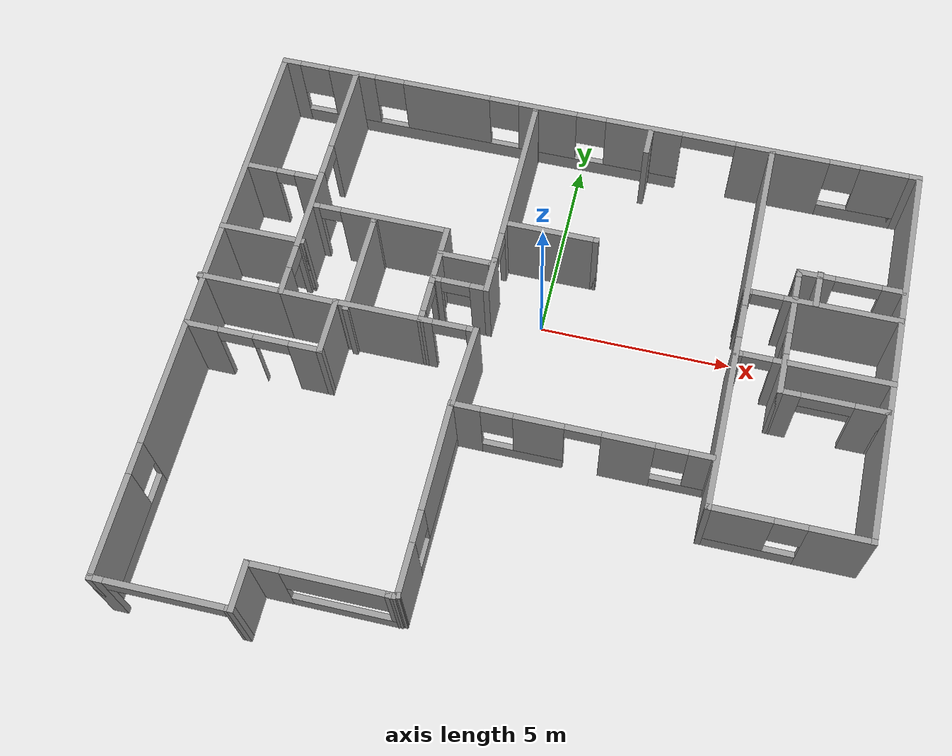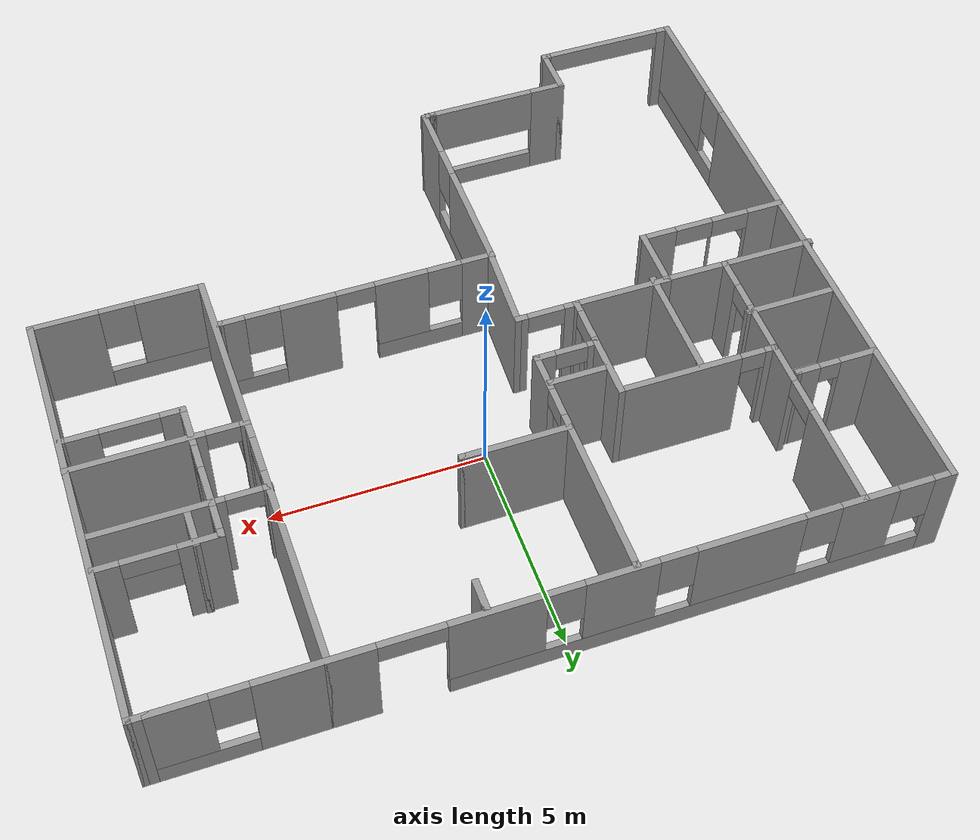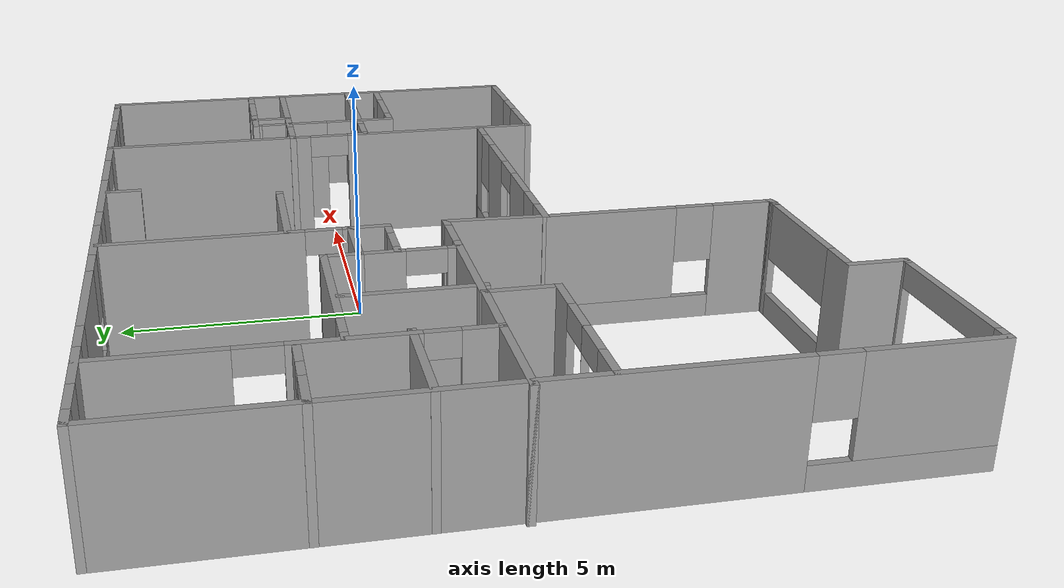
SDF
<?xml version='1.0'?>
<sdf version='1.7'>
  <model name='Floorplan7'>
    <pose>0.227488 -2.2016 0 0 -0 0</pose>
    <link name='Wall_0'>
      <pose>-0.133018 7.425 0 0 -0 0</pose>
      <visual name='Wall_0_Visual_0'>
        <pose>-8.24103 0 1.25 0 -0 0</pose>
        <geometry>
          <box>
            <size>0.517936 0.15 2.5</size>
          </box>
        </geometry>
        <material>
          <script>
            <uri>file://media/materials/scripts/gazebo.material</uri>
            <name>Gazebo/Grey</name>
          </script>
          <ambient>1 1 1 1</ambient>
        </material>
        <meta>
          <layer>0</layer>
        </meta>
      </visual>
      <collision name='Wall_0_Collision_0'>
        <geometry>
          <box>
            <size>0.517936 0.15 2.5</size>
          </box>
        </geometry>
        <pose>-8.24103 0 1.25 0 -0 0</pose>
      </collision>
      <visual name='Wall_0_Visual_1'>
        <pose>5.19319 0 1.25 0 -0 0</pose>
        <geometry>
          <box>
            <size>2.48084 0.15 2.5</size>
          </box>
        </geometry>
        <material>
          <script>
            <uri>file://media/materials/scripts/gazebo.material</uri>
            <name>Gazebo/Grey</name>
          </script>
          <ambient>1 1 1 1</ambient>
        </material>
        <meta>
          <layer>0</layer>
        </meta>
      </visual>
      <collision name='Wall_0_Collision_1'>
        <geometry>
          <box>
            <size>2.48084 0.15 2.5</size>
          </box>
        </geometry>
        <pose>5.19319 0 1.25 0 -0 0</pose>
      </collision>
      <visual name='Wall_0_Visual_2'>
        <pose>-2.72761 0 0.25 0 -0 0</pose>
        <geometry>
          <box>
            <size>10.5089 0.15 0.5</size>
          </box>
        </geometry>
        <material>
          <script>
            <uri>file://media/materials/scripts/gazebo.material</uri>
            <name>Gazebo/Grey</name>
          </script>
          <ambient>1 1 1 1</ambient>
        </material>
        <meta>
          <layer>0</layer>
        </meta>
      </visual>
      <collision name='Wall_0_Collision_2'>
        <geometry>
          <box>
            <size>10.5089 0.15 0.5</size>
          </box>
        </geometry>
        <pose>-2.72761 0 0.25 0 -0 0</pose>
      </collision>
      <visual name='Wall_0_Visual_3'>
        <pose>7.4668 0 0.25 0 -0 0</pose>
        <geometry>
          <box>
            <size>2.06639 0.15 0.5</size>
          </box>
        </geometry>
        <material>
          <script>
            <uri>file://media/materials/scripts/gazebo.material</uri>
            <name>Gazebo/Grey</name>
          </script>
          <ambient>1 1 1 1</ambient>
        </material>
        <meta>
          <layer>0</layer>
        </meta>
      </visual>
      <collision name='Wall_0_Collision_3'>
        <geometry>
          <box>
            <size>2.06639 0.15 0.5</size>
          </box>
        </geometry>
        <pose>7.4668 0 0.25 0 -0 0</pose>
      </collision>
      <visual name='Wall_0_Visual_4'>
        <pose>-6.53696 0 1.5 0 -0 0</pose>
        <geometry>
          <box>
            <size>1.29021 0.15 2</size>
          </box>
        </geometry>
        <material>
          <script>
            <uri>file://media/materials/scripts/gazebo.material</uri>
            <name>Gazebo/Grey</name>
          </script>
          <ambient>1 1 1 1</ambient>
        </material>
        <meta>
          <layer>0</layer>
        </meta>
      </visual>
      <collision name='Wall_0_Collision_4'>
        <geometry>
          <box>
            <size>1.29021 0.15 2</size>
          </box>
        </geometry>
        <pose>-6.53696 0 1.5 0 -0 0</pose>
      </collision>
      <visual name='Wall_0_Visual_5'>
        <pose>-3.90061 0 1.5 0 -0 0</pose>
        <geometry>
          <box>
            <size>2.38251 0.15 2</size>
          </box>
        </geometry>
        <material>
          <script>
            <uri>file://media/materials/scripts/gazebo.material</uri>
            <name>Gazebo/Grey</name>
          </script>
          <ambient>1 1 1 1</ambient>
        </material>
        <meta>
          <layer>0</layer>
        </meta>
      </visual>
      <collision name='Wall_0_Collision_5'>
        <geometry>
          <box>
            <size>2.38251 0.15 2</size>
          </box>
        </geometry>
        <pose>-3.90061 0 1.5 0 -0 0</pose>
      </collision>
      <visual name='Wall_0_Visual_6'>
        <pose>-1.11591 0 1.5 0 -0 0</pose>
        <geometry>
          <box>
            <size>1.58688 0.15 2</size>
          </box>
        </geometry>
        <material>
          <script>
            <uri>file://media/materials/scripts/gazebo.material</uri>
            <name>Gazebo/Grey</name>
          </script>
          <ambient>1 1 1 1</ambient>
        </material>
        <meta>
          <layer>0</layer>
        </meta>
      </visual>
      <collision name='Wall_0_Collision_6'>
        <geometry>
          <box>
            <size>1.58688 0.15 2</size>
          </box>
        </geometry>
        <pose>-1.11591 0 1.5 0 -0 0</pose>
      </collision>
      <visual name='Wall_0_Visual_7'>
        <pose>1.50218 0 1.5 0 -0 0</pose>
        <geometry>
          <box>
            <size>2.04932 0.15 2</size>
          </box>
        </geometry>
        <material>
          <script>
            <uri>file://media/materials/scripts/gazebo.material</uri>
            <name>Gazebo/Grey</name>
          </script>
          <ambient>1 1 1 1</ambient>
        </material>
        <meta>
          <layer>0</layer>
        </meta>
      </visual>
      <collision name='Wall_0_Collision_7'>
        <geometry>
          <box>
            <size>2.04932 0.15 2</size>
          </box>
        </geometry>
        <pose>1.50218 0 1.5 0 -0 0</pose>
      </collision>
      <visual name='Wall_0_Visual_8'>
        <pose>1.50218 0 1.5 0 -0 0</pose>
        <geometry>
          <box>
            <size>2.04932 0.15 2</size>
          </box>
        </geometry>
        <material>
          <script>
            <uri>file://media/materials/scripts/gazebo.material</uri>
            <name>Gazebo/Grey</name>
          </script>
          <ambient>1 1 1 1</ambient>
        </material>
        <meta>
          <layer>0</layer>
        </meta>
      </visual>
      <collision name='Wall_0_Collision_8'>
        <geometry>
          <box>
            <size>2.04932 0.15 2</size>
          </box>
        </geometry>
        <pose>1.50218 0 1.5 0 -0 0</pose>
      </collision>
      <visual name='Wall_0_Visual_9'>
        <pose>7.8668 0 1.5 0 -0 0</pose>
        <geometry>
          <box>
            <size>1.26639 0.15 2</size>
          </box>
        </geometry>
        <material>
          <script>
            <uri>file://media/materials/scripts/gazebo.material</uri>
            <name>Gazebo/Grey</name>
          </script>
          <ambient>1 1 1 1</ambient>
        </material>
        <meta>
          <layer>0</layer>
        </meta>
      </visual>
      <collision name='Wall_0_Collision_9'>
        <geometry>
          <box>
            <size>1.26639 0.15 2</size>
          </box>
        </geometry>
        <pose>7.8668 0 1.5 0 -0 0</pose>
      </collision>
      <visual name='Wall_0_Visual_10'>
        <pose>-7.58206 0 1.9 0 -0 0</pose>
        <geometry>
          <box>
            <size>0.8 0.15 1.2</size>
          </box>
        </geometry>
        <material>
          <script>
            <uri>file://media/materials/scripts/gazebo.material</uri>
            <name>Gazebo/Grey</name>
          </script>
          <ambient>1 1 1 1</ambient>
        </material>
        <meta>
          <layer>0</layer>
        </meta>
      </visual>
      <collision name='Wall_0_Collision_10'>
        <geometry>
          <box>
            <size>0.8 0.15 1.2</size>
          </box>
        </geometry>
        <pose>-7.58206 0 1.9 0 -0 0</pose>
      </collision>
      <visual name='Wall_0_Visual_11'>
        <pose>6.83361 0 1.9 0 -0 0</pose>
        <geometry>
          <box>
            <size>0.8 0.15 1.2</size>
          </box>
        </geometry>
        <material>
          <script>
            <uri>file://media/materials/scripts/gazebo.material</uri>
            <name>Gazebo/Grey</name>
          </script>
          <ambient>1 1 1 1</ambient>
        </material>
        <meta>
          <layer>0</layer>
        </meta>
      </visual>
      <collision name='Wall_0_Collision_11'>
        <geometry>
          <box>
            <size>0.8 0.15 1.2</size>
          </box>
        </geometry>
        <pose>6.83361 0 1.9 0 -0 0</pose>
      </collision>
      <visual name='Wall_0_Visual_12'>
        <pose>-5.49186 0 1.9 0 -0 0</pose>
        <geometry>
          <box>
            <size>0.8 0.15 1.2</size>
          </box>
        </geometry>
        <material>
          <script>
            <uri>file://media/materials/scripts/gazebo.material</uri>
            <name>Gazebo/Grey</name>
          </script>
          <ambient>1 1 1 1</ambient>
        </material>
        <meta>
          <layer>0</layer>
        </meta>
      </visual>
      <collision name='Wall_0_Collision_12'>
        <geometry>
          <box>
            <size>0.8 0.15 1.2</size>
          </box>
        </geometry>
        <pose>-5.49186 0 1.9 0 -0 0</pose>
      </collision>
      <visual name='Wall_0_Visual_13'>
        <pose>-2.30935 0 1.9 0 -0 0</pose>
        <geometry>
          <box>
            <size>0.8 0.15 1.2</size>
          </box>
        </geometry>
        <material>
          <script>
            <uri>file://media/materials/scripts/gazebo.material</uri>
            <name>Gazebo/Grey</name>
          </script>
          <ambient>1 1 1 1</ambient>
        </material>
        <meta>
          <layer>0</layer>
        </meta>
      </visual>
      <collision name='Wall_0_Collision_13'>
        <geometry>
          <box>
            <size>0.8 0.15 1.2</size>
          </box>
        </geometry>
        <pose>-2.30935 0 1.9 0 -0 0</pose>
      </collision>
      <visual name='Wall_0_Visual_14'>
        <pose>0.077526 0 1.9 0 -0 0</pose>
        <geometry>
          <box>
            <size>0.8 0.15 1.2</size>
          </box>
        </geometry>
        <material>
          <script>
            <uri>file://media/materials/scripts/gazebo.material</uri>
            <name>Gazebo/Grey</name>
          </script>
          <ambient>1 1 1 1</ambient>
        </material>
        <meta>
          <layer>0</layer>
        </meta>
      </visual>
      <collision name='Wall_0_Collision_14'>
        <geometry>
          <box>
            <size>0.8 0.15 1.2</size>
          </box>
        </geometry>
        <pose>0.077526 0 1.9 0 -0 0</pose>
      </collision>
      <visual name='Wall_0_Visual_15'>
        <pose>3.2398 0 2.25 0 -0 0</pose>
        <geometry>
          <box>
            <size>1.42592 0.15 0.5</size>
          </box>
        </geometry>
        <material>
          <script>
            <uri>file://media/materials/scripts/gazebo.material</uri>
            <name>Gazebo/Grey</name>
          </script>
          <ambient>1 1 1 1</ambient>
        </material>
        <meta>
          <layer>0</layer>
        </meta>
      </visual>
      <collision name='Wall_0_Collision_15'>
        <geometry>
          <box>
            <size>1.42592 0.15 0.5</size>
          </box>
        </geometry>
        <pose>3.2398 0 2.25 0 -0 0</pose>
      </collision>
      <visual name='Wall_0_Visual_16'>
        <pose>3.2398 0 2.25 0 -0 0</pose>
        <geometry>
          <box>
            <size>1.42592 0.15 0.5</size>
          </box>
        </geometry>
        <material>
          <script>
            <uri>file://media/materials/scripts/gazebo.material</uri>
            <name>Gazebo/Grey</name>
          </script>
          <ambient>1 1 1 1</ambient>
        </material>
        <meta>
          <layer>0</layer>
        </meta>
      </visual>
      <collision name='Wall_0_Collision_16'>
        <geometry>
          <box>
            <size>1.42592 0.15 0.5</size>
          </box>
        </geometry>
        <pose>3.2398 0 2.25 0 -0 0</pose>
      </collision>
    </link>
    <link name='Wall_1'>
      <collision name='Wall_1_Collision'>
        <geometry>
          <box>
            <size>0.5 0.15 2.5</size>
          </box>
        </geometry>
        <pose>0 0 1.25 0 -0 0</pose>
      </collision>
      <visual name='Wall_1_Visual'>
        <pose>0 0 1.25 0 -0 0</pose>
        <geometry>
          <box>
            <size>0.5 0.15 2.5</size>
          </box>
        </geometry>
        <material>
          <script>
            <uri>file://media/materials/scripts/gazebo.material</uri>
            <name>Gazebo/Grey</name>
          </script>
          <ambient>1 1 1 1</ambient>
        </material>
        <meta>
          <layer>0</layer>
        </meta>
      </visual>
      <pose>8.46698 7.425 0 0 -0 0</pose>
    </link>
    <link name='Wall_10'>
      <collision name='Wall_10_Collision'>
        <geometry>
          <box>
            <size>1.25 0.15 2.5</size>
          </box>
        </geometry>
        <pose>0 0 1.25 0 -0 0</pose>
      </collision>
      <visual name='Wall_10_Visual'>
        <pose>0 0 1.25 0 -0 0</pose>
        <geometry>
          <box>
            <size>1.25 0.15 2.5</size>
          </box>
        </geometry>
        <material>
          <script>
            <uri>file://media/materials/scripts/gazebo.material</uri>
            <name>Gazebo/Grey</name>
          </script>
          <ambient>1 1 1 1</ambient>
        </material>
        <meta>
          <layer>0</layer>
        </meta>
      </visual>
      <pose>-5.20802 -6.875 0 0 -0 1.5708</pose>
    </link>
    <link name='Wall_11'>
      <pose>-3.53302 -6.325 0 0 -0 0</pose>
      <visual name='Wall_11_Visual_0'>
        <pose>-1.31856 0 1.25 0 -0 0</pose>
        <geometry>
          <box>
            <size>0.862879 0.15 2.5</size>
          </box>
        </geometry>
        <material>
          <script>
            <uri>file://media/materials/scripts/gazebo.material</uri>
            <name>Gazebo/Grey</name>
          </script>
          <ambient>1 1 1 1</ambient>
        </material>
        <meta>
          <layer>0</layer>
        </meta>
      </visual>
      <collision name='Wall_11_Collision_0'>
        <geometry>
          <box>
            <size>0.862879 0.15 2.5</size>
          </box>
        </geometry>
        <pose>-1.31856 0 1.25 0 -0 0</pose>
      </collision>
      <visual name='Wall_11_Visual_1'>
        <pose>0.43144 0 0.25 0 -0 0</pose>
        <geometry>
          <box>
            <size>2.63712 0.15 0.5</size>
          </box>
        </geometry>
        <material>
          <script>
            <uri>file://media/materials/scripts/gazebo.material</uri>
            <name>Gazebo/Grey</name>
          </script>
          <ambient>1 1 1 1</ambient>
        </material>
        <meta>
          <layer>0</layer>
        </meta>
      </visual>
      <collision name='Wall_11_Collision_1'>
        <geometry>
          <box>
            <size>2.63712 0.15 0.5</size>
          </box>
        </geometry>
        <pose>0.43144 0 0.25 0 -0 0</pose>
      </collision>
      <visual name='Wall_11_Visual_2'>
        <pose>1.67426 0 1.5 0 -0 0</pose>
        <geometry>
          <box>
            <size>0.151472 0.15 2</size>
          </box>
        </geometry>
        <material>
          <script>
            <uri>file://media/materials/scripts/gazebo.material</uri>
            <name>Gazebo/Grey</name>
          </script>
          <ambient>1 1 1 1</ambient>
        </material>
        <meta>
          <layer>0</layer>
        </meta>
      </visual>
      <collision name='Wall_11_Collision_2'>
        <geometry>
          <box>
            <size>0.151472 0.15 2</size>
          </box>
        </geometry>
        <pose>1.67426 0 1.5 0 -0 0</pose>
      </collision>
      <visual name='Wall_11_Visual_3'>
        <pose>0.355704 0 1.9 0 -0 0</pose>
        <geometry>
          <box>
            <size>2.48565 0.15 1.2</size>
          </box>
        </geometry>
        <material>
          <script>
            <uri>file://media/materials/scripts/gazebo.material</uri>
            <name>Gazebo/Grey</name>
          </script>
          <ambient>1 1 1 1</ambient>
        </material>
        <meta>
          <layer>0</layer>
        </meta>
      </visual>
      <collision name='Wall_11_Collision_3'>
        <geometry>
          <box>
            <size>2.48565 0.15 1.2</size>
          </box>
        </geometry>
        <pose>0.355704 0 1.9 0 -0 0</pose>
      </collision>
    </link>
    <link name='Wall_12'>
      <collision name='Wall_12_Collision'>
        <geometry>
          <box>
            <size>0.25 0.15 2.5</size>
          </box>
        </geometry>
        <pose>0 0 1.25 0 -0 0</pose>
      </collision>
      <visual name='Wall_12_Visual'>
        <pose>0 0 1.25 0 -0 0</pose>
        <geometry>
          <box>
            <size>0.25 0.15 2.5</size>
          </box>
        </geometry>
        <material>
          <script>
            <uri>file://media/materials/scripts/gazebo.material</uri>
            <name>Gazebo/Grey</name>
          </script>
          <ambient>1 1 1 1</ambient>
        </material>
        <meta>
          <layer>0</layer>
        </meta>
      </visual>
      <pose>-1.80802 -6.325 0 0 -0 0</pose>
    </link>
    <link name='Wall_13'>
      <collision name='Wall_13_Collision'>
        <geometry>
          <box>
            <size>0.25 0.15 2.5</size>
          </box>
        </geometry>
        <pose>0 0 1.25 0 -0 0</pose>
      </collision>
      <visual name='Wall_13_Visual'>
        <pose>0 0 1.25 0 -0 0</pose>
        <geometry>
          <box>
            <size>0.25 0.15 2.5</size>
          </box>
        </geometry>
        <material>
          <script>
            <uri>file://media/materials/scripts/gazebo.material</uri>
            <name>Gazebo/Grey</name>
          </script>
          <ambient>1 1 1 1</ambient>
        </material>
        <meta>
          <layer>0</layer>
        </meta>
      </visual>
      <pose>-1.70972 -6.31206 0 0 -0 0.261799</pose>
    </link>
    <link name='Wall_14'>
      <pose>-1.65681 -3.87627 0 0 -0 1.56889</pose>
      <visual name='Wall_14_Visual_0'>
        <pose>-1.82183 0 1.25 0 -0 0</pose>
        <geometry>
          <box>
            <size>1.35207 0.15 2.5</size>
          </box>
        </geometry>
        <material>
          <script>
            <uri>file://media/materials/scripts/gazebo.material</uri>
            <name>Gazebo/Grey</name>
          </script>
          <ambient>1 1 1 1</ambient>
        </material>
        <meta>
          <layer>0</layer>
        </meta>
      </visual>
      <collision name='Wall_14_Collision_0'>
        <geometry>
          <box>
            <size>1.35207 0.15 2.5</size>
          </box>
        </geometry>
        <pose>-1.82183 0 1.25 0 -0 0</pose>
      </collision>
      <visual name='Wall_14_Visual_1'>
        <pose>0.676036 0 0.25 0 -0 0</pose>
        <geometry>
          <box>
            <size>3.64367 0.15 0.5</size>
          </box>
        </geometry>
        <material>
          <script>
            <uri>file://media/materials/scripts/gazebo.material</uri>
            <name>Gazebo/Grey</name>
          </script>
          <ambient>1 1 1 1</ambient>
        </material>
        <meta>
          <layer>0</layer>
        </meta>
      </visual>
      <collision name='Wall_14_Collision_1'>
        <geometry>
          <box>
            <size>3.64367 0.15 0.5</size>
          </box>
        </geometry>
        <pose>0.676036 0 0.25 0 -0 0</pose>
      </collision>
      <visual name='Wall_14_Visual_2'>
        <pose>1.07604 0 1.5 0 -0 0</pose>
        <geometry>
          <box>
            <size>2.84367 0.15 2</size>
          </box>
        </geometry>
        <material>
          <script>
            <uri>file://media/materials/scripts/gazebo.material</uri>
            <name>Gazebo/Grey</name>
          </script>
          <ambient>1 1 1 1</ambient>
        </material>
        <meta>
          <layer>0</layer>
        </meta>
      </visual>
      <collision name='Wall_14_Collision_2'>
        <geometry>
          <box>
            <size>2.84367 0.15 2</size>
          </box>
        </geometry>
        <pose>1.07604 0 1.5 0 -0 0</pose>
      </collision>
      <visual name='Wall_14_Visual_3'>
        <pose>-0.745799 0 1.9 0 -0 0</pose>
        <geometry>
          <box>
            <size>0.8 0.15 1.2</size>
          </box>
        </geometry>
        <material>
          <script>
            <uri>file://media/materials/scripts/gazebo.material</uri>
            <name>Gazebo/Grey</name>
          </script>
          <ambient>1 1 1 1</ambient>
        </material>
        <meta>
          <layer>0</layer>
        </meta>
      </visual>
      <collision name='Wall_14_Collision_3'>
        <geometry>
          <box>
            <size>0.8 0.15 1.2</size>
          </box>
        </geometry>
        <pose>-0.745799 0 1.9 0 -0 0</pose>
      </collision>
    </link>
    <link name='Wall_15'>
      <pose>1.51819 -1.45127 0 0 -0 0.00068</pose>
      <visual name='Wall_15_Visual_0'>
        <pose>-2.84549 0 1.25 0 -0 0</pose>
        <geometry>
          <box>
            <size>0.799793 0.15 2.5</size>
          </box>
        </geometry>
        <material>
          <script>
            <uri>file://media/materials/scripts/gazebo.material</uri>
            <name>Gazebo/Grey</name>
          </script>
          <ambient>1 1 1 1</ambient>
        </material>
        <meta>
          <layer>0</layer>
        </meta>
      </visual>
      <collision name='Wall_15_Collision_0'>
        <geometry>
          <box>
            <size>0.799793 0.15 2.5</size>
          </box>
        </geometry>
        <pose>-2.84549 0 1.25 0 -0 0</pose>
      </collision>
      <visual name='Wall_15_Visual_1'>
        <pose>1.15507 0 1.25 0 -0 0</pose>
        <geometry>
          <box>
            <size>1.29419 0.15 2.5</size>
          </box>
        </geometry>
        <material>
          <script>
            <uri>file://media/materials/scripts/gazebo.material</uri>
            <name>Gazebo/Grey</name>
          </script>
          <ambient>1 1 1 1</ambient>
        </material>
        <meta>
          <layer>0</layer>
        </meta>
      </visual>
      <collision name='Wall_15_Collision_1'>
        <geometry>
          <box>
            <size>1.29419 0.15 2.5</size>
          </box>
        </geometry>
        <pose>1.15507 0 1.25 0 -0 0</pose>
      </collision>
      <visual name='Wall_15_Visual_2'>
        <pose>-1.41881 0 0.25 0 -0 0</pose>
        <geometry>
          <box>
            <size>2.05357 0.15 0.5</size>
          </box>
        </geometry>
        <material>
          <script>
            <uri>file://media/materials/scripts/gazebo.material</uri>
            <name>Gazebo/Grey</name>
          </script>
          <ambient>1 1 1 1</ambient>
        </material>
        <meta>
          <layer>0</layer>
        </meta>
      </visual>
      <collision name='Wall_15_Collision_2'>
        <geometry>
          <box>
            <size>2.05357 0.15 0.5</size>
          </box>
        </geometry>
        <pose>-1.41881 0 0.25 0 -0 0</pose>
      </collision>
      <visual name='Wall_15_Visual_3'>
        <pose>2.52378 0 0.25 0 -0 0</pose>
        <geometry>
          <box>
            <size>1.44322 0.15 0.5</size>
          </box>
        </geometry>
        <material>
          <script>
            <uri>file://media/materials/scripts/gazebo.material</uri>
            <name>Gazebo/Grey</name>
          </script>
          <ambient>1 1 1 1</ambient>
        </material>
        <meta>
          <layer>0</layer>
        </meta>
      </visual>
      <collision name='Wall_15_Collision_3'>
        <geometry>
          <box>
            <size>1.44322 0.15 0.5</size>
          </box>
        </geometry>
        <pose>2.52378 0 0.25 0 -0 0</pose>
      </collision>
      <visual name='Wall_15_Visual_4'>
        <pose>-1.01881 0 1.5 0 -0 0</pose>
        <geometry>
          <box>
            <size>1.25357 0.15 2</size>
          </box>
        </geometry>
        <material>
          <script>
            <uri>file://media/materials/scripts/gazebo.material</uri>
            <name>Gazebo/Grey</name>
          </script>
          <ambient>1 1 1 1</ambient>
        </material>
        <meta>
          <layer>0</layer>
        </meta>
      </visual>
      <collision name='Wall_15_Collision_4'>
        <geometry>
          <box>
            <size>1.25357 0.15 2</size>
          </box>
        </geometry>
        <pose>-1.01881 0 1.5 0 -0 0</pose>
      </collision>
      <visual name='Wall_15_Visual_5'>
        <pose>-1.01881 0 1.5 0 -0 0</pose>
        <geometry>
          <box>
            <size>1.25357 0.15 2</size>
          </box>
        </geometry>
        <material>
          <script>
            <uri>file://media/materials/scripts/gazebo.material</uri>
            <name>Gazebo/Grey</name>
          </script>
          <ambient>1 1 1 1</ambient>
        </material>
        <meta>
          <layer>0</layer>
        </meta>
      </visual>
      <collision name='Wall_15_Collision_5'>
        <geometry>
          <box>
            <size>1.25357 0.15 2</size>
          </box>
        </geometry>
        <pose>-1.01881 0 1.5 0 -0 0</pose>
      </collision>
      <visual name='Wall_15_Visual_6'>
        <pose>2.92378 0 1.5 0 -0 0</pose>
        <geometry>
          <box>
            <size>0.643216 0.15 2</size>
          </box>
        </geometry>
        <material>
          <script>
            <uri>file://media/materials/scripts/gazebo.material</uri>
            <name>Gazebo/Grey</name>
          </script>
          <ambient>1 1 1 1</ambient>
        </material>
        <meta>
          <layer>0</layer>
        </meta>
      </visual>
      <collision name='Wall_15_Collision_6'>
        <geometry>
          <box>
            <size>0.643216 0.15 2</size>
          </box>
        </geometry>
        <pose>2.92378 0 1.5 0 -0 0</pose>
      </collision>
      <visual name='Wall_15_Visual_7'>
        <pose>-2.04559 0 1.9 0 -0 0</pose>
        <geometry>
          <box>
            <size>0.8 0.15 1.2</size>
          </box>
        </geometry>
        <material>
          <script>
            <uri>file://media/materials/scripts/gazebo.material</uri>
            <name>Gazebo/Grey</name>
          </script>
          <ambient>1 1 1 1</ambient>
        </material>
        <meta>
          <layer>0</layer>
        </meta>
      </visual>
      <collision name='Wall_15_Collision_7'>
        <geometry>
          <box>
            <size>0.8 0.15 1.2</size>
          </box>
        </geometry>
        <pose>-2.04559 0 1.9 0 -0 0</pose>
      </collision>
      <visual name='Wall_15_Visual_8'>
        <pose>2.20217 0 1.9 0 -0 0</pose>
        <geometry>
          <box>
            <size>0.8 0.15 1.2</size>
          </box>
        </geometry>
        <material>
          <script>
            <uri>file://media/materials/scripts/gazebo.material</uri>
            <name>Gazebo/Grey</name>
          </script>
          <ambient>1 1 1 1</ambient>
        </material>
        <meta>
          <layer>0</layer>
        </meta>
      </visual>
      <collision name='Wall_15_Collision_8'>
        <geometry>
          <box>
            <size>0.8 0.15 1.2</size>
          </box>
        </geometry>
        <pose>2.20217 0 1.9 0 -0 0</pose>
      </collision>
      <visual name='Wall_15_Visual_9'>
        <pose>0.057978 0 2.25 0 -0 0</pose>
        <geometry>
          <box>
            <size>0.9 0.15 0.5</size>
          </box>
        </geometry>
        <material>
          <script>
            <uri>file://media/materials/scripts/gazebo.material</uri>
            <name>Gazebo/Grey</name>
          </script>
          <ambient>1 1 1 1</ambient>
        </material>
        <meta>
          <layer>0</layer>
        </meta>
      </visual>
      <collision name='Wall_15_Collision_9'>
        <geometry>
          <box>
            <size>0.9 0.15 0.5</size>
          </box>
        </geometry>
        <pose>0.057978 0 2.25 0 -0 0</pose>
      </collision>
      <visual name='Wall_15_Visual_10'>
        <pose>0.057978 0 2.25 0 -0 0</pose>
        <geometry>
          <box>
            <size>0.9 0.15 0.5</size>
          </box>
        </geometry>
        <material>
          <script>
            <uri>file://media/materials/scripts/gazebo.material</uri>
            <name>Gazebo/Grey</name>
          </script>
          <ambient>1 1 1 1</ambient>
        </material>
        <meta>
          <layer>0</layer>
        </meta>
      </visual>
      <collision name='Wall_15_Collision_10'>
        <geometry>
          <box>
            <size>0.9 0.15 0.5</size>
          </box>
        </geometry>
        <pose>0.057978 0 2.25 0 -0 0</pose>
      </collision>
    </link>
    <link name='Wall_16'>
      <collision name='Wall_16_Collision'>
        <geometry>
          <box>
            <size>0.15 0.15 2.5</size>
          </box>
        </geometry>
        <pose>0 0 1.25 0 -0 0</pose>
      </collision>
      <visual name='Wall_16_Visual'>
        <pose>0 0 1.25 0 -0 0</pose>
        <geometry>
          <box>
            <size>0.15 0.15 2.5</size>
          </box>
        </geometry>
        <material>
          <script>
            <uri>file://media/materials/scripts/gazebo.material</uri>
            <name>Gazebo/Grey</name>
          </script>
          <ambient>1 1 1 1</ambient>
        </material>
        <meta>
          <layer>0</layer>
        </meta>
      </visual>
      <pose>4.68858 -1.44912 0 0 -0 0</pose>
    </link>
    <link name='Wall_18'>
      <pose>-6.54918 3.98735 0 0 -0 -1.5708</pose>
      <visual name='Wall_18_Visual_0'>
        <pose>-2.2619 0 1.25 0 -0 0</pose>
        <geometry>
          <box>
            <size>2.47621 0.15 2.5</size>
          </box>
        </geometry>
        <material>
          <script>
            <uri>file://media/materials/scripts/gazebo.material</uri>
            <name>Gazebo/Grey</name>
          </script>
          <ambient>1 1 1 1</ambient>
        </material>
        <meta>
          <layer>0</layer>
        </meta>
      </visual>
      <collision name='Wall_18_Collision_0'>
        <geometry>
          <box>
            <size>2.47621 0.15 2.5</size>
          </box>
        </geometry>
        <pose>-2.2619 0 1.25 0 -0 0</pose>
      </collision>
      <visual name='Wall_18_Visual_1'>
        <pose>0.956775 0 1.25 0 -0 0</pose>
        <geometry>
          <box>
            <size>2.26902 0.15 2.5</size>
          </box>
        </geometry>
        <material>
          <script>
            <uri>file://media/materials/scripts/gazebo.material</uri>
            <name>Gazebo/Grey</name>
          </script>
          <ambient>1 1 1 1</ambient>
        </material>
        <meta>
          <layer>0</layer>
        </meta>
      </visual>
      <collision name='Wall_18_Collision_1'>
        <geometry>
          <box>
            <size>2.26902 0.15 2.5</size>
          </box>
        </geometry>
        <pose>0.956775 0 1.25 0 -0 0</pose>
      </collision>
      <visual name='Wall_18_Visual_2'>
        <pose>3.11753 0 1.25 0 -0 0</pose>
        <geometry>
          <box>
            <size>0.764934 0.15 2.5</size>
          </box>
        </geometry>
        <material>
          <script>
            <uri>file://media/materials/scripts/gazebo.material</uri>
            <name>Gazebo/Grey</name>
          </script>
          <ambient>1 1 1 1</ambient>
        </material>
        <meta>
          <layer>0</layer>
        </meta>
      </visual>
      <collision name='Wall_18_Collision_2'>
        <geometry>
          <box>
            <size>0.764934 0.15 2.5</size>
          </box>
        </geometry>
        <pose>3.11753 0 1.25 0 -0 0</pose>
      </collision>
      <visual name='Wall_18_Visual_3'>
        <pose>-0.600765 0 2.25 0 -0 0</pose>
        <geometry>
          <box>
            <size>0.846059 0.15 0.5</size>
          </box>
        </geometry>
        <material>
          <script>
            <uri>file://media/materials/scripts/gazebo.material</uri>
            <name>Gazebo/Grey</name>
          </script>
          <ambient>1 1 1 1</ambient>
        </material>
        <meta>
          <layer>0</layer>
        </meta>
      </visual>
      <collision name='Wall_18_Collision_3'>
        <geometry>
          <box>
            <size>0.846059 0.15 0.5</size>
          </box>
        </geometry>
        <pose>-0.600765 0 2.25 0 -0 0</pose>
      </collision>
      <visual name='Wall_18_Visual_4'>
        <pose>2.41317 0 2.25 0 -0 0</pose>
        <geometry>
          <box>
            <size>0.643781 0.15 0.5</size>
          </box>
        </geometry>
        <material>
          <script>
            <uri>file://media/materials/scripts/gazebo.material</uri>
            <name>Gazebo/Grey</name>
          </script>
          <ambient>1 1 1 1</ambient>
        </material>
        <meta>
          <layer>0</layer>
        </meta>
      </visual>
      <collision name='Wall_18_Collision_4'>
        <geometry>
          <box>
            <size>0.643781 0.15 0.5</size>
          </box>
        </geometry>
        <pose>2.41317 0 2.25 0 -0 0</pose>
      </collision>
    </link>
    <link name='Wall_19'>
      <collision name='Wall_19_Collision'>
        <geometry>
          <box>
            <size>2.25 0.15 2.5</size>
          </box>
        </geometry>
        <pose>0 0 1.25 0 -0 0</pose>
      </collision>
      <visual name='Wall_19_Visual'>
        <pose>0 0 1.25 0 -0 0</pose>
        <geometry>
          <box>
            <size>2.25 0.15 2.5</size>
          </box>
        </geometry>
        <material>
          <script>
            <uri>file://media/materials/scripts/gazebo.material</uri>
            <name>Gazebo/Grey</name>
          </script>
          <ambient>1 1 1 1</ambient>
        </material>
        <meta>
          <layer>0</layer>
        </meta>
      </visual>
      <pose>-7.59918 0.562349 0 0 -0 3.14159</pose>
    </link>
    <link name='Wall_2'>
      <collision name='Wall_2_Collision'>
        <geometry>
          <box>
            <size>10.25 0.15 2.5</size>
          </box>
        </geometry>
        <pose>0 0 1.25 0 -0 0</pose>
      </collision>
      <visual name='Wall_2_Visual'>
        <pose>0 0 1.25 0 -0 0</pose>
        <geometry>
          <box>
            <size>10.25 0.15 2.5</size>
          </box>
        </geometry>
        <material>
          <script>
            <uri>file://media/materials/scripts/gazebo.material</uri>
            <name>Gazebo/Grey</name>
          </script>
          <ambient>1 1 1 1</ambient>
        </material>
        <meta>
          <layer>0</layer>
        </meta>
      </visual>
      <pose>8.64198 2.375 0 0 -0 -1.5708</pose>
    </link>
    <link name='Wall_20'>
      <collision name='Wall_20_Collision'>
        <geometry>
          <box>
            <size>0.15 0.15 2.5</size>
          </box>
        </geometry>
        <pose>0 0 1.25 0 -0 0</pose>
      </collision>
      <visual name='Wall_20_Visual'>
        <pose>0 0 1.25 0 -0 0</pose>
        <geometry>
          <box>
            <size>0.15 0.15 2.5</size>
          </box>
        </geometry>
        <material>
          <script>
            <uri>file://media/materials/scripts/gazebo.material</uri>
            <name>Gazebo/Grey</name>
          </script>
          <ambient>1 1 1 1</ambient>
        </material>
        <meta>
          <layer>0</layer>
        </meta>
      </visual>
      <pose>-8.64918 0.562349 0 0 -0 0</pose>
    </link>
    <link name='Wall_22'>
      <pose>-6.83525 -0.793988 0 0 -0 0</pose>
      <visual name='Wall_22_Visual_0'>
        <pose>-1.33924 0 1.25 0 -0 0</pose>
        <geometry>
          <box>
            <size>0.881865 0.15 2.5</size>
          </box>
        </geometry>
        <material>
          <script>
            <uri>file://media/materials/scripts/gazebo.material</uri>
            <name>Gazebo/Grey</name>
          </script>
          <ambient>1 1 1 1</ambient>
        </material>
        <meta>
          <layer>0</layer>
        </meta>
      </visual>
      <collision name='Wall_22_Collision_0'>
        <geometry>
          <box>
            <size>0.881865 0.15 2.5</size>
          </box>
        </geometry>
        <pose>-1.33924 0 1.25 0 -0 0</pose>
      </collision>
      <visual name='Wall_22_Visual_1'>
        <pose>0.003448 0 1.25 0 -0 0</pose>
        <geometry>
          <box>
            <size>0.003508 0.15 2.5</size>
          </box>
        </geometry>
        <material>
          <script>
            <uri>file://media/materials/scripts/gazebo.material</uri>
            <name>Gazebo/Grey</name>
          </script>
          <ambient>1 1 1 1</ambient>
        </material>
        <meta>
          <layer>0</layer>
        </meta>
      </visual>
      <collision name='Wall_22_Collision_1'>
        <geometry>
          <box>
            <size>0.003508 0.15 2.5</size>
          </box>
        </geometry>
        <pose>0.003448 0 1.25 0 -0 0</pose>
      </collision>
      <visual name='Wall_22_Visual_2'>
        <pose>1.34269 0 1.25 0 -0 0</pose>
        <geometry>
          <box>
            <size>0.874968 0.15 2.5</size>
          </box>
        </geometry>
        <material>
          <script>
            <uri>file://media/materials/scripts/gazebo.material</uri>
            <name>Gazebo/Grey</name>
          </script>
          <ambient>1 1 1 1</ambient>
        </material>
        <meta>
          <layer>0</layer>
        </meta>
      </visual>
      <collision name='Wall_22_Collision_2'>
        <geometry>
          <box>
            <size>0.874968 0.15 2.5</size>
          </box>
        </geometry>
        <pose>1.34269 0 1.25 0 -0 0</pose>
      </collision>
      <visual name='Wall_22_Visual_3'>
        <pose>-0.448306 0 2.25 0 -0 0</pose>
        <geometry>
          <box>
            <size>0.9 0.15 0.5</size>
          </box>
        </geometry>
        <material>
          <script>
            <uri>file://media/materials/scripts/gazebo.material</uri>
            <name>Gazebo/Grey</name>
          </script>
          <ambient>1 1 1 1</ambient>
        </material>
        <meta>
          <layer>0</layer>
        </meta>
      </visual>
      <collision name='Wall_22_Collision_3'>
        <geometry>
          <box>
            <size>0.9 0.15 0.5</size>
          </box>
        </geometry>
        <pose>-0.448306 0 2.25 0 -0 0</pose>
      </collision>
      <visual name='Wall_22_Visual_4'>
        <pose>0.455202 0 2.25 0 -0 0</pose>
        <geometry>
          <box>
            <size>0.9 0.15 0.5</size>
          </box>
        </geometry>
        <material>
          <script>
            <uri>file://media/materials/scripts/gazebo.material</uri>
            <name>Gazebo/Grey</name>
          </script>
          <ambient>1 1 1 1</ambient>
        </material>
        <meta>
          <layer>0</layer>
        </meta>
      </visual>
      <collision name='Wall_22_Collision_4'>
        <geometry>
          <box>
            <size>0.9 0.15 0.5</size>
          </box>
        </geometry>
        <pose>0.455202 0 2.25 0 -0 0</pose>
      </collision>
    </link>
    <link name='Wall_23'>
      <collision name='Wall_23_Collision'>
        <geometry>
          <box>
            <size>1.5 0.15 2.5</size>
          </box>
        </geometry>
        <pose>0 0 1.25 0 -0 0</pose>
      </collision>
      <visual name='Wall_23_Visual'>
        <pose>0 0 1.25 0 -0 0</pose>
        <geometry>
          <box>
            <size>1.5 0.15 2.5</size>
          </box>
        </geometry>
        <material>
          <script>
            <uri>file://media/materials/scripts/gazebo.material</uri>
            <name>Gazebo/Grey</name>
          </script>
          <ambient>1 1 1 1</ambient>
        </material>
        <meta>
          <layer>0</layer>
        </meta>
      </visual>
      <pose>-5.13008 -0.118989 0 0 -0 1.5708</pose>
    </link>
    <link name='Wall_24'>
      <collision name='Wall_24_Collision'>
        <geometry>
          <box>
            <size>1.56911 0.15 2.5</size>
          </box>
        </geometry>
        <pose>0 0 1.25 0 -0 0</pose>
      </collision>
      <visual name='Wall_24_Visual'>
        <pose>0 0 1.25 0 -0 0</pose>
        <geometry>
          <box>
            <size>1.56911 0.15 2.5</size>
          </box>
        </geometry>
        <material>
          <script>
            <uri>file://media/materials/scripts/gazebo.material</uri>
            <name>Gazebo/Grey</name>
          </script>
          <ambient>1 1 1 1</ambient>
        </material>
        <meta>
          <layer>0</layer>
        </meta>
      </visual>
      <pose>-5.83963 0.55918 0 0 -0 3.13713</pose>
    </link>
    <link name='Wall_25'>
      <collision name='Wall_25_Collision'>
        <geometry>
          <box>
            <size>0.15 0.15 2.5</size>
          </box>
        </geometry>
        <pose>0 0 1.25 0 -0 0</pose>
      </collision>
      <visual name='Wall_25_Visual'>
        <pose>0 0 1.25 0 -0 0</pose>
        <geometry>
          <box>
            <size>0.15 0.15 2.5</size>
          </box>
        </geometry>
        <material>
          <script>
            <uri>file://media/materials/scripts/gazebo.material</uri>
            <name>Gazebo/Grey</name>
          </script>
          <ambient>1 1 1 1</ambient>
        </material>
        <meta>
          <layer>0</layer>
        </meta>
      </visual>
      <pose>-6.54918 0.562349 0 0 -0 0</pose>
    </link>
    <link name='Wall_27'>
      <collision name='Wall_27_Collision'>
        <geometry>
          <box>
            <size>2.25 0.15 2.5</size>
          </box>
        </geometry>
        <pose>0 0 1.25 0 -0 0</pose>
      </collision>
      <visual name='Wall_27_Visual'>
        <pose>0 0 1.25 0 -0 0</pose>
        <geometry>
          <box>
            <size>2.25 0.15 2.5</size>
          </box>
        </geometry>
        <material>
          <script>
            <uri>file://media/materials/scripts/gazebo.material</uri>
            <name>Gazebo/Grey</name>
          </script>
          <ambient>1 1 1 1</ambient>
        </material>
        <meta>
          <layer>0</layer>
        </meta>
      </visual>
      <pose>-7.51053 2.06214 0 0 -0 0</pose>
    </link>
    <link name='Wall_28'>
      <collision name='Wall_28_Collision'>
        <geometry>
          <box>
            <size>0.15 0.15 2.5</size>
          </box>
        </geometry>
        <pose>0 0 1.25 0 -0 0</pose>
      </collision>
      <visual name='Wall_28_Visual'>
        <pose>0 0 1.25 0 -0 0</pose>
        <geometry>
          <box>
            <size>0.15 0.15 2.5</size>
          </box>
        </geometry>
        <material>
          <script>
            <uri>file://media/materials/scripts/gazebo.material</uri>
            <name>Gazebo/Grey</name>
          </script>
          <ambient>1 1 1 1</ambient>
        </material>
        <meta>
          <layer>0</layer>
        </meta>
      </visual>
      <pose>-6.46053 2.06214 0 0 -0 0</pose>
    </link>
    <link name='Wall_3'>
      <collision name='Wall_3_Collision'>
        <geometry>
          <box>
            <size>0.15 0.15 2.5</size>
          </box>
        </geometry>
        <pose>0 0 1.25 0 -0 0</pose>
      </collision>
      <visual name='Wall_3_Visual'>
        <pose>0 0 1.25 0 -0 0</pose>
        <geometry>
          <box>
            <size>0.15 0.15 2.5</size>
          </box>
        </geometry>
        <material>
          <script>
            <uri>file://media/materials/scripts/gazebo.material</uri>
            <name>Gazebo/Grey</name>
          </script>
          <ambient>1 1 1 1</ambient>
        </material>
        <meta>
          <layer>0</layer>
        </meta>
      </visual>
      <pose>8.64198 -2.675 0 0 -0 0</pose>
    </link>
    <link name='Wall_30'>
      <pose>-7.63553 3.97293 0 0 -0 0</pose>
      <visual name='Wall_30_Visual_0'>
        <pose>-0.538897 0 1.25 0 -0 0</pose>
        <geometry>
          <box>
            <size>0.922206 0.15 2.5</size>
          </box>
        </geometry>
        <material>
          <script>
            <uri>file://media/materials/scripts/gazebo.material</uri>
            <name>Gazebo/Grey</name>
          </script>
          <ambient>1 1 1 1</ambient>
        </material>
        <meta>
          <layer>0</layer>
        </meta>
      </visual>
      <collision name='Wall_30_Collision_0'>
        <geometry>
          <box>
            <size>0.922206 0.15 2.5</size>
          </box>
        </geometry>
        <pose>-0.538897 0 1.25 0 -0 0</pose>
      </collision>
      <visual name='Wall_30_Visual_1'>
        <pose>0.702083 0 1.25 0 -0 0</pose>
        <geometry>
          <box>
            <size>0.595835 0.15 2.5</size>
          </box>
        </geometry>
        <material>
          <script>
            <uri>file://media/materials/scripts/gazebo.material</uri>
            <name>Gazebo/Grey</name>
          </script>
          <ambient>1 1 1 1</ambient>
        </material>
        <meta>
          <layer>0</layer>
        </meta>
      </visual>
      <collision name='Wall_30_Collision_1'>
        <geometry>
          <box>
            <size>0.595835 0.15 2.5</size>
          </box>
        </geometry>
        <pose>0.702083 0 1.25 0 -0 0</pose>
      </collision>
      <visual name='Wall_30_Visual_2'>
        <pose>0.163186 0 2.25 0 -0 0</pose>
        <geometry>
          <box>
            <size>0.481959 0.15 0.5</size>
          </box>
        </geometry>
        <material>
          <script>
            <uri>file://media/materials/scripts/gazebo.material</uri>
            <name>Gazebo/Grey</name>
          </script>
          <ambient>1 1 1 1</ambient>
        </material>
        <meta>
          <layer>0</layer>
        </meta>
      </visual>
      <collision name='Wall_30_Collision_2'>
        <geometry>
          <box>
            <size>0.481959 0.15 0.5</size>
          </box>
        </geometry>
        <pose>0.163186 0 2.25 0 -0 0</pose>
      </collision>
    </link>
    <link name='Wall_31'>
      <collision name='Wall_31_Collision'>
        <geometry>
          <box>
            <size>0.15 0.15 2.5</size>
          </box>
        </geometry>
        <pose>0 0 1.25 0 -0 0</pose>
      </collision>
      <visual name='Wall_31_Visual'>
        <pose>0 0 1.25 0 -0 0</pose>
        <geometry>
          <box>
            <size>0.15 0.15 2.5</size>
          </box>
        </geometry>
        <material>
          <script>
            <uri>file://media/materials/scripts/gazebo.material</uri>
            <name>Gazebo/Grey</name>
          </script>
          <ambient>1 1 1 1</ambient>
        </material>
        <meta>
          <layer>0</layer>
        </meta>
      </visual>
      <pose>-6.71053 3.97293 0 0 -0 0</pose>
    </link>
    <link name='Wall_33'>
      <pose>-4.7387 3.17612 0 0 -0 0</pose>
      <visual name='Wall_33_Visual_0'>
        <pose>-1.71604 0 1.25 0 -0 0</pose>
        <geometry>
          <box>
            <size>0.287751 0.15 2.5</size>
          </box>
        </geometry>
        <material>
          <script>
            <uri>file://media/materials/scripts/gazebo.material</uri>
            <name>Gazebo/Grey</name>
          </script>
          <ambient>1 1 1 1</ambient>
        </material>
        <meta>
          <layer>0</layer>
        </meta>
      </visual>
      <collision name='Wall_33_Collision_0'>
        <geometry>
          <box>
            <size>0.287751 0.15 2.5</size>
          </box>
        </geometry>
        <pose>-1.71604 0 1.25 0 -0 0</pose>
      </collision>
      <visual name='Wall_33_Visual_1'>
        <pose>0.42531 0 1.25 0 -0 0</pose>
        <geometry>
          <box>
            <size>2.86921 0.15 2.5</size>
          </box>
        </geometry>
        <material>
          <script>
            <uri>file://media/materials/scripts/gazebo.material</uri>
            <name>Gazebo/Grey</name>
          </script>
          <ambient>1 1 1 1</ambient>
        </material>
        <meta>
          <layer>0</layer>
        </meta>
      </visual>
      <collision name='Wall_33_Collision_1'>
        <geometry>
          <box>
            <size>2.86921 0.15 2.5</size>
          </box>
        </geometry>
        <pose>0.42531 0 1.25 0 -0 0</pose>
      </collision>
      <visual name='Wall_33_Visual_2'>
        <pose>-1.29073 0 2.25 0 -0 0</pose>
        <geometry>
          <box>
            <size>0.56287 0.15 0.5</size>
          </box>
        </geometry>
        <material>
          <script>
            <uri>file://media/materials/scripts/gazebo.material</uri>
            <name>Gazebo/Grey</name>
          </script>
          <ambient>1 1 1 1</ambient>
        </material>
        <meta>
          <layer>0</layer>
        </meta>
      </visual>
      <collision name='Wall_33_Collision_2'>
        <geometry>
          <box>
            <size>0.56287 0.15 0.5</size>
          </box>
        </geometry>
        <pose>-1.29073 0 2.25 0 -0 0</pose>
      </collision>
    </link>
    <link name='Wall_34'>
      <pose>-2.94373 1.87613 0 0 -0 -1.5708</pose>
      <visual name='Wall_34_Visual_0'>
        <pose>-0.559246 0 1.25 0 -0 0</pose>
        <geometry>
          <box>
            <size>1.63151 0.15 2.5</size>
          </box>
        </geometry>
        <material>
          <script>
            <uri>file://media/materials/scripts/gazebo.material</uri>
            <name>Gazebo/Grey</name>
          </script>
          <ambient>1 1 1 1</ambient>
        </material>
        <meta>
          <layer>0</layer>
        </meta>
      </visual>
      <collision name='Wall_34_Collision_0'>
        <geometry>
          <box>
            <size>1.63151 0.15 2.5</size>
          </box>
        </geometry>
        <pose>-0.559246 0 1.25 0 -0 0</pose>
      </collision>
      <visual name='Wall_34_Visual_1'>
        <pose>1.21856 0 1.25 0 -0 0</pose>
        <geometry>
          <box>
            <size>0.312889 0.15 2.5</size>
          </box>
        </geometry>
        <material>
          <script>
            <uri>file://media/materials/scripts/gazebo.material</uri>
            <name>Gazebo/Grey</name>
          </script>
          <ambient>1 1 1 1</ambient>
        </material>
        <meta>
          <layer>0</layer>
        </meta>
      </visual>
      <collision name='Wall_34_Collision_1'>
        <geometry>
          <box>
            <size>0.312889 0.15 2.5</size>
          </box>
        </geometry>
        <pose>1.21856 0 1.25 0 -0 0</pose>
      </collision>
      <visual name='Wall_34_Visual_2'>
        <pose>0.659309 0 2.25 0 -0 0</pose>
        <geometry>
          <box>
            <size>0.805604 0.15 0.5</size>
          </box>
        </geometry>
        <material>
          <script>
            <uri>file://media/materials/scripts/gazebo.material</uri>
            <name>Gazebo/Grey</name>
          </script>
          <ambient>1 1 1 1</ambient>
        </material>
        <meta>
          <layer>0</layer>
        </meta>
      </visual>
      <collision name='Wall_34_Collision_2'>
        <geometry>
          <box>
            <size>0.805604 0.15 0.5</size>
          </box>
        </geometry>
        <pose>0.659309 0 2.25 0 -0 0</pose>
      </collision>
    </link>
    <link name='Wall_35'>
      <collision name='Wall_35_Collision'>
        <geometry>
          <box>
            <size>2.33635 0.15 2.5</size>
          </box>
        </geometry>
        <pose>0 0 1.25 0 -0 0</pose>
      </collision>
      <visual name='Wall_35_Visual'>
        <pose>0 0 1.25 0 -0 0</pose>
        <geometry>
          <box>
            <size>2.33635 0.15 2.5</size>
          </box>
        </geometry>
        <material>
          <script>
            <uri>file://media/materials/scripts/gazebo.material</uri>
            <name>Gazebo/Grey</name>
          </script>
          <ambient>1 1 1 1</ambient>
        </material>
        <meta>
          <layer>0</layer>
        </meta>
      </visual>
      <pose>-4.03691 0.576125 0 0 -0 3.14159</pose>
    </link>
    <link name='Wall_36'>
      <collision name='Wall_36_Collision'>
        <geometry>
          <box>
            <size>0.15 0.15 2.5</size>
          </box>
        </geometry>
        <pose>0 0 1.25 0 -0 0</pose>
      </collision>
      <visual name='Wall_36_Visual'>
        <pose>0 0 1.25 0 -0 0</pose>
        <geometry>
          <box>
            <size>0.15 0.15 2.5</size>
          </box>
        </geometry>
        <material>
          <script>
            <uri>file://media/materials/scripts/gazebo.material</uri>
            <name>Gazebo/Grey</name>
          </script>
          <ambient>1 1 1 1</ambient>
        </material>
        <meta>
          <layer>0</layer>
        </meta>
      </visual>
      <pose>-5.13008 0.556011 0 0 -0 0</pose>
    </link>
    <link name='Wall_38'>
      <collision name='Wall_38_Collision'>
        <geometry>
          <box>
            <size>2.75 0.15 2.5</size>
          </box>
        </geometry>
        <pose>0 0 1.25 0 -0 0</pose>
      </collision>
      <visual name='Wall_38_Visual'>
        <pose>0 0 1.25 0 -0 0</pose>
        <geometry>
          <box>
            <size>2.75 0.15 2.5</size>
          </box>
        </geometry>
        <material>
          <script>
            <uri>file://media/materials/scripts/gazebo.material</uri>
            <name>Gazebo/Grey</name>
          </script>
          <ambient>1 1 1 1</ambient>
        </material>
        <meta>
          <layer>0</layer>
        </meta>
      </visual>
      <pose>-4.83903 1.77689 0 0 -0 1.5708</pose>
    </link>
    <link name='Wall_39'>
      <collision name='Wall_39_Collision'>
        <geometry>
          <box>
            <size>0.15 0.15 2.5</size>
          </box>
        </geometry>
        <pose>0 0 1.25 0 -0 0</pose>
      </collision>
      <visual name='Wall_39_Visual'>
        <pose>0 0 1.25 0 -0 0</pose>
        <geometry>
          <box>
            <size>0.15 0.15 2.5</size>
          </box>
        </geometry>
        <material>
          <script>
            <uri>file://media/materials/scripts/gazebo.material</uri>
            <name>Gazebo/Grey</name>
          </script>
          <ambient>1 1 1 1</ambient>
        </material>
        <meta>
          <layer>0</layer>
        </meta>
      </visual>
      <pose>-4.83903 3.07689 0 0 -0 0</pose>
    </link>
    <link name='Wall_4'>
      <pose>6.71698 -2.675 0 0 -0 3.14159</pose>
      <visual name='Wall_4_Visual_0'>
        <pose>-1.20529 0 1.25 0 -0 0</pose>
        <geometry>
          <box>
            <size>1.58942 0.15 2.5</size>
          </box>
        </geometry>
        <material>
          <script>
            <uri>file://media/materials/scripts/gazebo.material</uri>
            <name>Gazebo/Grey</name>
          </script>
          <ambient>1 1 1 1</ambient>
        </material>
        <meta>
          <layer>0</layer>
        </meta>
      </visual>
      <collision name='Wall_4_Collision_0'>
        <geometry>
          <box>
            <size>1.58942 0.15 2.5</size>
          </box>
        </geometry>
        <pose>-1.20529 0 1.25 0 -0 0</pose>
      </collision>
      <visual name='Wall_4_Visual_1'>
        <pose>0.794711 0 0.25 0 -0 0</pose>
        <geometry>
          <box>
            <size>2.41058 0.15 0.5</size>
          </box>
        </geometry>
        <material>
          <script>
            <uri>file://media/materials/scripts/gazebo.material</uri>
            <name>Gazebo/Grey</name>
          </script>
          <ambient>1 1 1 1</ambient>
        </material>
        <meta>
          <layer>0</layer>
        </meta>
      </visual>
      <collision name='Wall_4_Collision_1'>
        <geometry>
          <box>
            <size>2.41058 0.15 0.5</size>
          </box>
        </geometry>
        <pose>0.794711 0 0.25 0 -0 0</pose>
      </collision>
      <visual name='Wall_4_Visual_2'>
        <pose>1.19471 0 1.5 0 -0 0</pose>
        <geometry>
          <box>
            <size>1.61058 0.15 2</size>
          </box>
        </geometry>
        <material>
          <script>
            <uri>file://media/materials/scripts/gazebo.material</uri>
            <name>Gazebo/Grey</name>
          </script>
          <ambient>1 1 1 1</ambient>
        </material>
        <meta>
          <layer>0</layer>
        </meta>
      </visual>
      <collision name='Wall_4_Collision_2'>
        <geometry>
          <box>
            <size>1.61058 0.15 2</size>
          </box>
        </geometry>
        <pose>1.19471 0 1.5 0 -0 0</pose>
      </collision>
      <visual name='Wall_4_Visual_3'>
        <pose>-0.010578 0 1.9 0 -0 0</pose>
        <geometry>
          <box>
            <size>0.8 0.15 1.2</size>
          </box>
        </geometry>
        <material>
          <script>
            <uri>file://media/materials/scripts/gazebo.material</uri>
            <name>Gazebo/Grey</name>
          </script>
          <ambient>1 1 1 1</ambient>
        </material>
        <meta>
          <layer>0</layer>
        </meta>
      </visual>
      <collision name='Wall_4_Collision_3'>
        <geometry>
          <box>
            <size>0.8 0.15 1.2</size>
          </box>
        </geometry>
        <pose>-0.010578 0 1.9 0 -0 0</pose>
      </collision>
    </link>
    <link name='Wall_41'>
      <pose>-2.23312 1.76416 0 0 -0 0</pose>
      <visual name='Wall_41_Visual_0'>
        <pose>-0.620342 0 1.25 0 -0 0</pose>
        <geometry>
          <box>
            <size>0.259315 0.15 2.5</size>
          </box>
        </geometry>
        <material>
          <script>
            <uri>file://media/materials/scripts/gazebo.material</uri>
            <name>Gazebo/Grey</name>
          </script>
          <ambient>1 1 1 1</ambient>
        </material>
        <meta>
          <layer>0</layer>
        </meta>
      </visual>
      <collision name='Wall_41_Collision_0'>
        <geometry>
          <box>
            <size>0.259315 0.15 2.5</size>
          </box>
        </geometry>
        <pose>-0.620342 0 1.25 0 -0 0</pose>
      </collision>
      <visual name='Wall_41_Visual_1'>
        <pose>0.498746 0 1.25 0 -0 0</pose>
        <geometry>
          <box>
            <size>0.502507 0.15 2.5</size>
          </box>
        </geometry>
        <material>
          <script>
            <uri>file://media/materials/scripts/gazebo.material</uri>
            <name>Gazebo/Grey</name>
          </script>
          <ambient>1 1 1 1</ambient>
        </material>
        <meta>
          <layer>0</layer>
        </meta>
      </visual>
      <collision name='Wall_41_Collision_1'>
        <geometry>
          <box>
            <size>0.502507 0.15 2.5</size>
          </box>
        </geometry>
        <pose>0.498746 0 1.25 0 -0 0</pose>
      </collision>
      <visual name='Wall_41_Visual_2'>
        <pose>-0.121596 0 2.25 0 -0 0</pose>
        <geometry>
          <box>
            <size>0.738178 0.15 0.5</size>
          </box>
        </geometry>
        <material>
          <script>
            <uri>file://media/materials/scripts/gazebo.material</uri>
            <name>Gazebo/Grey</name>
          </script>
          <ambient>1 1 1 1</ambient>
        </material>
        <meta>
          <layer>0</layer>
        </meta>
      </visual>
      <collision name='Wall_41_Collision_2'>
        <geometry>
          <box>
            <size>0.738178 0.15 0.5</size>
          </box>
        </geometry>
        <pose>-0.121596 0 2.25 0 -0 0</pose>
      </collision>
    </link>
    <link name='Wall_42'>
      <pose>-1.55812 4.56416 0 0 -0 1.5708</pose>
      <visual name='Wall_42_Visual_0'>
        <pose>-2.38547 0 1.25 0 -0 0</pose>
        <geometry>
          <box>
            <size>0.979068 0.15 2.5</size>
          </box>
        </geometry>
        <material>
          <script>
            <uri>file://media/materials/scripts/gazebo.material</uri>
            <name>Gazebo/Grey</name>
          </script>
          <ambient>1 1 1 1</ambient>
        </material>
        <meta>
          <layer>0</layer>
        </meta>
      </visual>
      <collision name='Wall_42_Collision_0'>
        <geometry>
          <box>
            <size>0.979068 0.15 2.5</size>
          </box>
        </geometry>
        <pose>-2.38547 0 1.25 0 -0 0</pose>
      </collision>
      <visual name='Wall_42_Visual_1'>
        <pose>0.858623 0 1.25 0 -0 0</pose>
        <geometry>
          <box>
            <size>4.03275 0.15 2.5</size>
          </box>
        </geometry>
        <material>
          <script>
            <uri>file://media/materials/scripts/gazebo.material</uri>
            <name>Gazebo/Grey</name>
          </script>
          <ambient>1 1 1 1</ambient>
        </material>
        <meta>
          <layer>0</layer>
        </meta>
      </visual>
      <collision name='Wall_42_Collision_1'>
        <geometry>
          <box>
            <size>4.03275 0.15 2.5</size>
          </box>
        </geometry>
        <pose>0.858623 0 1.25 0 -0 0</pose>
      </collision>
      <visual name='Wall_42_Visual_2'>
        <pose>-1.52684 0 2.25 0 -0 0</pose>
        <geometry>
          <box>
            <size>0.738178 0.15 0.5</size>
          </box>
        </geometry>
        <material>
          <script>
            <uri>file://media/materials/scripts/gazebo.material</uri>
            <name>Gazebo/Grey</name>
          </script>
          <ambient>1 1 1 1</ambient>
        </material>
        <meta>
          <layer>0</layer>
        </meta>
      </visual>
      <collision name='Wall_42_Collision_2'>
        <geometry>
          <box>
            <size>0.738178 0.15 0.5</size>
          </box>
        </geometry>
        <pose>-1.52684 0 2.25 0 -0 0</pose>
      </collision>
    </link>
    <link name='Wall_43'>
      <collision name='Wall_43_Collision'>
        <geometry>
          <box>
            <size>0.15 0.15 2.5</size>
          </box>
        </geometry>
        <pose>0 0 1.25 0 -0 0</pose>
      </collision>
      <visual name='Wall_43_Visual'>
        <pose>0 0 1.25 0 -0 0</pose>
        <geometry>
          <box>
            <size>0.15 0.15 2.5</size>
          </box>
        </geometry>
        <material>
          <script>
            <uri>file://media/materials/scripts/gazebo.material</uri>
            <name>Gazebo/Grey</name>
          </script>
          <ambient>1 1 1 1</ambient>
        </material>
        <meta>
          <layer>0</layer>
        </meta>
      </visual>
      <pose>-1.55812 7.36416 0 0 -0 0</pose>
    </link>
    <link name='Wall_45'>
      <collision name='Wall_45_Collision'>
        <geometry>
          <box>
            <size>1.5 0.15 2.5</size>
          </box>
        </geometry>
        <pose>0 0 1.25 0 -0 0</pose>
      </collision>
      <visual name='Wall_45_Visual'>
        <pose>0 0 1.25 0 -0 0</pose>
        <geometry>
          <box>
            <size>1.5 0.15 2.5</size>
          </box>
        </geometry>
        <material>
          <script>
            <uri>file://media/materials/scripts/gazebo.material</uri>
            <name>Gazebo/Grey</name>
          </script>
          <ambient>1 1 1 1</ambient>
        </material>
        <meta>
          <layer>0</layer>
        </meta>
      </visual>
      <pose>-2.27785 2.49435 0 0 -0 0</pose>
    </link>
    <link name='Wall_46'>
      <collision name='Wall_46_Collision'>
        <geometry>
          <box>
            <size>0.15 0.15 2.5</size>
          </box>
        </geometry>
        <pose>0 0 1.25 0 -0 0</pose>
      </collision>
      <visual name='Wall_46_Visual'>
        <pose>0 0 1.25 0 -0 0</pose>
        <geometry>
          <box>
            <size>0.15 0.15 2.5</size>
          </box>
        </geometry>
        <material>
          <script>
            <uri>file://media/materials/scripts/gazebo.material</uri>
            <name>Gazebo/Grey</name>
          </script>
          <ambient>1 1 1 1</ambient>
        </material>
        <meta>
          <layer>0</layer>
        </meta>
      </visual>
      <pose>-1.60285 2.49435 0 0 -0 0</pose>
    </link>
    <link name='Wall_48'>
      <collision name='Wall_48_Collision'>
        <geometry>
          <box>
            <size>2.5 0.15 2.5</size>
          </box>
        </geometry>
        <pose>0 0 1.25 0 -0 0</pose>
      </collision>
      <visual name='Wall_48_Visual'>
        <pose>0 0 1.25 0 -0 0</pose>
        <geometry>
          <box>
            <size>2.5 0.15 2.5</size>
          </box>
        </geometry>
        <material>
          <script>
            <uri>file://media/materials/scripts/gazebo.material</uri>
            <name>Gazebo/Grey</name>
          </script>
          <ambient>1 1 1 1</ambient>
        </material>
        <meta>
          <layer>0</layer>
        </meta>
      </visual>
      <pose>-0.362057 3.73766 0 0 -0 0</pose>
    </link>
    <link name='Wall_49'>
      <collision name='Wall_49_Collision'>
        <geometry>
          <box>
            <size>0.15 0.15 2.5</size>
          </box>
        </geometry>
        <pose>0 0 1.25 0 -0 0</pose>
      </collision>
      <visual name='Wall_49_Visual'>
        <pose>0 0 1.25 0 -0 0</pose>
        <geometry>
          <box>
            <size>0.15 0.15 2.5</size>
          </box>
        </geometry>
        <material>
          <script>
            <uri>file://media/materials/scripts/gazebo.material</uri>
            <name>Gazebo/Grey</name>
          </script>
          <ambient>1 1 1 1</ambient>
        </material>
        <meta>
          <layer>0</layer>
        </meta>
      </visual>
      <pose>0.824508 3.73766 0 0 -0 0</pose>
    </link>
    <link name='Wall_5'>
      <pose>4.79198 2.375 0 0 -0 1.5708</pose>
      <visual name='Wall_5_Visual_0'>
        <pose>-2.83659 0 1.25 0 -0 0</pose>
        <geometry>
          <box>
            <size>4.57682 0.15 2.5</size>
          </box>
        </geometry>
        <material>
          <script>
            <uri>file://media/materials/scripts/gazebo.material</uri>
            <name>Gazebo/Grey</name>
          </script>
          <ambient>1 1 1 1</ambient>
        </material>
        <meta>
          <layer>0</layer>
        </meta>
      </visual>
      <collision name='Wall_5_Collision_0'>
        <geometry>
          <box>
            <size>4.57682 0.15 2.5</size>
          </box>
        </geometry>
        <pose>-2.83659 0 1.25 0 -0 0</pose>
      </collision>
      <visual name='Wall_5_Visual_1'>
        <pose>2.73841 0 1.25 0 -0 0</pose>
        <geometry>
          <box>
            <size>4.77318 0.15 2.5</size>
          </box>
        </geometry>
        <material>
          <script>
            <uri>file://media/materials/scripts/gazebo.material</uri>
            <name>Gazebo/Grey</name>
          </script>
          <ambient>1 1 1 1</ambient>
        </material>
        <meta>
          <layer>0</layer>
        </meta>
      </visual>
      <collision name='Wall_5_Collision_1'>
        <geometry>
          <box>
            <size>4.77318 0.15 2.5</size>
          </box>
        </geometry>
        <pose>2.73841 0 1.25 0 -0 0</pose>
      </collision>
      <visual name='Wall_5_Visual_2'>
        <pose>-0.098182 0 2.25 0 -0 0</pose>
        <geometry>
          <box>
            <size>0.9 0.15 0.5</size>
          </box>
        </geometry>
        <material>
          <script>
            <uri>file://media/materials/scripts/gazebo.material</uri>
            <name>Gazebo/Grey</name>
          </script>
          <ambient>1 1 1 1</ambient>
        </material>
        <meta>
          <layer>0</layer>
        </meta>
      </visual>
      <collision name='Wall_5_Collision_2'>
        <geometry>
          <box>
            <size>0.9 0.15 0.5</size>
          </box>
        </geometry>
        <pose>-0.098182 0 2.25 0 -0 0</pose>
      </collision>
    </link>
    <link name='Wall_51'>
      <pose>-2.251 0.578342 0 0 -0 0.0032</pose>
      <visual name='Wall_51_Visual_0'>
        <pose>-0.57981 0 1.25 0 -0 0</pose>
        <geometry>
          <box>
            <size>0.375855 0.15 2.5</size>
          </box>
        </geometry>
        <material>
          <script>
            <uri>file://media/materials/scripts/gazebo.material</uri>
            <name>Gazebo/Grey</name>
          </script>
          <ambient>1 1 1 1</ambient>
        </material>
        <meta>
          <layer>0</layer>
        </meta>
      </visual>
      <collision name='Wall_51_Collision_0'>
        <geometry>
          <box>
            <size>0.375855 0.15 2.5</size>
          </box>
        </geometry>
        <pose>-0.57981 0 1.25 0 -0 0</pose>
      </collision>
      <visual name='Wall_51_Visual_1'>
        <pose>0.6177 0 1.25 0 -0 0</pose>
        <geometry>
          <box>
            <size>0.300075 0.15 2.5</size>
          </box>
        </geometry>
        <material>
          <script>
            <uri>file://media/materials/scripts/gazebo.material</uri>
            <name>Gazebo/Grey</name>
          </script>
          <ambient>1 1 1 1</ambient>
        </material>
        <meta>
          <layer>0</layer>
        </meta>
      </visual>
      <collision name='Wall_51_Collision_1'>
        <geometry>
          <box>
            <size>0.300075 0.15 2.5</size>
          </box>
        </geometry>
        <pose>0.6177 0 1.25 0 -0 0</pose>
      </collision>
      <visual name='Wall_51_Visual_2'>
        <pose>0.03789 0 2.25 0 -0 0</pose>
        <geometry>
          <box>
            <size>0.859545 0.15 0.5</size>
          </box>
        </geometry>
        <material>
          <script>
            <uri>file://media/materials/scripts/gazebo.material</uri>
            <name>Gazebo/Grey</name>
          </script>
          <ambient>1 1 1 1</ambient>
        </material>
        <meta>
          <layer>0</layer>
        </meta>
      </visual>
      <collision name='Wall_51_Collision_2'>
        <geometry>
          <box>
            <size>0.859545 0.15 0.5</size>
          </box>
        </geometry>
        <pose>0.03789 0 2.25 0 -0 0</pose>
      </collision>
    </link>
    <link name='Wall_52'>
      <collision name='Wall_52_Collision'>
        <geometry>
          <box>
            <size>2.18615 0.15 2.5</size>
          </box>
        </geometry>
        <pose>0 0 1.25 0 -0 0</pose>
      </collision>
      <visual name='Wall_52_Visual'>
        <pose>0 0 1.25 0 -0 0</pose>
        <geometry>
          <box>
            <size>2.18615 0.15 2.5</size>
          </box>
        </geometry>
        <material>
          <script>
            <uri>file://media/materials/scripts/gazebo.material</uri>
            <name>Gazebo/Grey</name>
          </script>
          <ambient>1 1 1 1</ambient>
        </material>
        <meta>
          <layer>0</layer>
        </meta>
      </visual>
      <pose>-1.59193 -0.432002 0 0 -0 -1.61694</pose>
    </link>
    <link name='Wall_53'>
      <collision name='Wall_53_Collision'>
        <geometry>
          <box>
            <size>0.15 0.15 2.5</size>
          </box>
        </geometry>
        <pose>0 0 1.25 0 -0 0</pose>
      </collision>
      <visual name='Wall_53_Visual'>
        <pose>0 0 1.25 0 -0 0</pose>
        <geometry>
          <box>
            <size>0.15 0.15 2.5</size>
          </box>
        </geometry>
        <material>
          <script>
            <uri>file://media/materials/scripts/gazebo.material</uri>
            <name>Gazebo/Grey</name>
          </script>
          <ambient>1 1 1 1</ambient>
        </material>
        <meta>
          <layer>0</layer>
        </meta>
      </visual>
      <pose>-1.65219 -1.45343 0 0 -0 0</pose>
    </link>
    <link name='Wall_55'>
      <collision name='Wall_55_Collision'>
        <geometry>
          <box>
            <size>0.75 0.15 2.5</size>
          </box>
        </geometry>
        <pose>0 0 1.25 0 -0 0</pose>
      </collision>
      <visual name='Wall_55_Visual'>
        <pose>0 0 1.25 0 -0 0</pose>
        <geometry>
          <box>
            <size>0.75 0.15 2.5</size>
          </box>
        </geometry>
        <material>
          <script>
            <uri>file://media/materials/scripts/gazebo.material</uri>
            <name>Gazebo/Grey</name>
          </script>
          <ambient>1 1 1 1</ambient>
        </material>
        <meta>
          <layer>0</layer>
        </meta>
      </visual>
      <pose>1.56273 7.00529 0 0 -0 1.5708</pose>
    </link>
    <link name='Wall_56'>
      <collision name='Wall_56_Collision'>
        <geometry>
          <box>
            <size>0.15 0.15 2.5</size>
          </box>
        </geometry>
        <pose>0 0 1.25 0 -0 0</pose>
      </collision>
      <visual name='Wall_56_Visual'>
        <pose>0 0 1.25 0 -0 0</pose>
        <geometry>
          <box>
            <size>0.15 0.15 2.5</size>
          </box>
        </geometry>
        <material>
          <script>
            <uri>file://media/materials/scripts/gazebo.material</uri>
            <name>Gazebo/Grey</name>
          </script>
          <ambient>1 1 1 1</ambient>
        </material>
        <meta>
          <layer>0</layer>
        </meta>
      </visual>
      <pose>1.56273 7.30529 0 0 -0 0</pose>
    </link>
    <link name='Wall_58'>
      <pose>7.28852 3.9678 0 0 -0 3.14159</pose>
      <visual name='Wall_58_Visual_0'>
        <pose>-1.07366 0 1.25 0 -0 0</pose>
        <geometry>
          <box>
            <size>0.602677 0.15 2.5</size>
          </box>
        </geometry>
        <material>
          <script>
            <uri>file://media/materials/scripts/gazebo.material</uri>
            <name>Gazebo/Grey</name>
          </script>
          <ambient>1 1 1 1</ambient>
        </material>
        <meta>
          <layer>0</layer>
        </meta>
      </visual>
      <collision name='Wall_58_Collision_0'>
        <geometry>
          <box>
            <size>0.602677 0.15 2.5</size>
          </box>
        </geometry>
        <pose>-1.07366 0 1.25 0 -0 0</pose>
      </collision>
      <visual name='Wall_58_Visual_1'>
        <pose>0.88619 0 1.25 0 -0 0</pose>
        <geometry>
          <box>
            <size>0.977619 0.15 2.5</size>
          </box>
        </geometry>
        <material>
          <script>
            <uri>file://media/materials/scripts/gazebo.material</uri>
            <name>Gazebo/Grey</name>
          </script>
          <ambient>1 1 1 1</ambient>
        </material>
        <meta>
          <layer>0</layer>
        </meta>
      </visual>
      <collision name='Wall_58_Collision_1'>
        <geometry>
          <box>
            <size>0.977619 0.15 2.5</size>
          </box>
        </geometry>
        <pose>0.88619 0 1.25 0 -0 0</pose>
      </collision>
      <visual name='Wall_58_Visual_2'>
        <pose>-0.187471 0 2.25 0 -0 0</pose>
        <geometry>
          <box>
            <size>1.1697 0.15 0.5</size>
          </box>
        </geometry>
        <material>
          <script>
            <uri>file://media/materials/scripts/gazebo.material</uri>
            <name>Gazebo/Grey</name>
          </script>
          <ambient>1 1 1 1</ambient>
        </material>
        <meta>
          <layer>0</layer>
        </meta>
      </visual>
      <collision name='Wall_58_Collision_2'>
        <geometry>
          <box>
            <size>1.1697 0.15 0.5</size>
          </box>
        </geometry>
        <pose>-0.187471 0 2.25 0 -0 0</pose>
      </collision>
    </link>
    <link name='Wall_59'>
      <pose>5.98852 2.29279 0 0 -0 -1.5708</pose>
      <visual name='Wall_59_Visual_0'>
        <pose>-1.64083 0 1.25 0 -0 0</pose>
        <geometry>
          <box>
            <size>0.218348 0.15 2.5</size>
          </box>
        </geometry>
        <material>
          <script>
            <uri>file://media/materials/scripts/gazebo.material</uri>
            <name>Gazebo/Grey</name>
          </script>
          <ambient>1 1 1 1</ambient>
        </material>
        <meta>
          <layer>0</layer>
        </meta>
      </visual>
      <collision name='Wall_59_Collision_0'>
        <geometry>
          <box>
            <size>0.218348 0.15 2.5</size>
          </box>
        </geometry>
        <pose>-1.64083 0 1.25 0 -0 0</pose>
      </collision>
      <visual name='Wall_59_Visual_1'>
        <pose>-0.437734 0 1.25 0 -0 0</pose>
        <geometry>
          <box>
            <size>1.03513 0.15 2.5</size>
          </box>
        </geometry>
        <material>
          <script>
            <uri>file://media/materials/scripts/gazebo.material</uri>
            <name>Gazebo/Grey</name>
          </script>
          <ambient>1 1 1 1</ambient>
        </material>
        <meta>
          <layer>0</layer>
        </meta>
      </visual>
      <collision name='Wall_59_Collision_1'>
        <geometry>
          <box>
            <size>1.03513 0.15 2.5</size>
          </box>
        </geometry>
        <pose>-0.437734 0 1.25 0 -0 0</pose>
      </collision>
      <visual name='Wall_59_Visual_2'>
        <pose>1.20983 0 1.25 0 -0 0</pose>
        <geometry>
          <box>
            <size>1.08033 0.15 2.5</size>
          </box>
        </geometry>
        <material>
          <script>
            <uri>file://media/materials/scripts/gazebo.material</uri>
            <name>Gazebo/Grey</name>
          </script>
          <ambient>1 1 1 1</ambient>
        </material>
        <meta>
          <layer>0</layer>
        </meta>
      </visual>
      <collision name='Wall_59_Collision_2'>
        <geometry>
          <box>
            <size>1.08033 0.15 2.5</size>
          </box>
        </geometry>
        <pose>1.20983 0 1.25 0 -0 0</pose>
      </collision>
      <visual name='Wall_59_Visual_3'>
        <pose>-1.24347 0 2.25 0 -0 0</pose>
        <geometry>
          <box>
            <size>0.576355 0.15 0.5</size>
          </box>
        </geometry>
        <material>
          <script>
            <uri>file://media/materials/scripts/gazebo.material</uri>
            <name>Gazebo/Grey</name>
          </script>
          <ambient>1 1 1 1</ambient>
        </material>
        <meta>
          <layer>0</layer>
        </meta>
      </visual>
      <collision name='Wall_59_Collision_3'>
        <geometry>
          <box>
            <size>0.576355 0.15 0.5</size>
          </box>
        </geometry>
        <pose>-1.24347 0 2.25 0 -0 0</pose>
      </collision>
      <visual name='Wall_59_Visual_4'>
        <pose>0.374749 0 2.25 0 -0 0</pose>
        <geometry>
          <box>
            <size>0.589841 0.15 0.5</size>
          </box>
        </geometry>
        <material>
          <script>
            <uri>file://media/materials/scripts/gazebo.material</uri>
            <name>Gazebo/Grey</name>
          </script>
          <ambient>1 1 1 1</ambient>
        </material>
        <meta>
          <layer>0</layer>
        </meta>
      </visual>
      <collision name='Wall_59_Collision_4'>
        <geometry>
          <box>
            <size>0.589841 0.15 0.5</size>
          </box>
        </geometry>
        <pose>0.374749 0 2.25 0 -0 0</pose>
      </collision>
    </link>
    <link name='Wall_6'>
      <collision name='Wall_6_Collision'>
        <geometry>
          <box>
            <size>0.15 0.15 2.5</size>
          </box>
        </geometry>
        <pose>0 0 1.25 0 -0 0</pose>
      </collision>
      <visual name='Wall_6_Visual'>
        <pose>0 0 1.25 0 -0 0</pose>
        <geometry>
          <box>
            <size>0.15 0.15 2.5</size>
          </box>
        </geometry>
        <material>
          <script>
            <uri>file://media/materials/scripts/gazebo.material</uri>
            <name>Gazebo/Grey</name>
          </script>
          <ambient>1 1 1 1</ambient>
        </material>
        <meta>
          <layer>0</layer>
        </meta>
      </visual>
      <pose>4.79198 7.425 0 0 -0 0</pose>
    </link>
    <link name='Wall_60'>
      <pose>7.28852 0.617795 0 0 -0 0</pose>
      <visual name='Wall_60_Visual_0'>
        <pose>-1.08847 0 1.25 0 -0 0</pose>
        <geometry>
          <box>
            <size>0.573064 0.15 2.5</size>
          </box>
        </geometry>
        <material>
          <script>
            <uri>file://media/materials/scripts/gazebo.material</uri>
            <name>Gazebo/Grey</name>
          </script>
          <ambient>1 1 1 1</ambient>
        </material>
        <meta>
          <layer>0</layer>
        </meta>
      </visual>
      <collision name='Wall_60_Collision_0'>
        <geometry>
          <box>
            <size>0.573064 0.15 2.5</size>
          </box>
        </geometry>
        <pose>-1.08847 0 1.25 0 -0 0</pose>
      </collision>
      <visual name='Wall_60_Visual_1'>
        <pose>0.93881 0 1.25 0 -0 0</pose>
        <geometry>
          <box>
            <size>0.87238 0.15 2.5</size>
          </box>
        </geometry>
        <material>
          <script>
            <uri>file://media/materials/scripts/gazebo.material</uri>
            <name>Gazebo/Grey</name>
          </script>
          <ambient>1 1 1 1</ambient>
        </material>
        <meta>
          <layer>0</layer>
        </meta>
      </visual>
      <collision name='Wall_60_Collision_1'>
        <geometry>
          <box>
            <size>0.87238 0.15 2.5</size>
          </box>
        </geometry>
        <pose>0.93881 0 1.25 0 -0 0</pose>
      </collision>
      <visual name='Wall_60_Visual_2'>
        <pose>-0.149658 0 2.25 0 -0 0</pose>
        <geometry>
          <box>
            <size>1.30456 0.15 0.5</size>
          </box>
        </geometry>
        <material>
          <script>
            <uri>file://media/materials/scripts/gazebo.material</uri>
            <name>Gazebo/Grey</name>
          </script>
          <ambient>1 1 1 1</ambient>
        </material>
        <meta>
          <layer>0</layer>
        </meta>
      </visual>
      <collision name='Wall_60_Collision_2'>
        <geometry>
          <box>
            <size>1.30456 0.15 0.5</size>
          </box>
        </geometry>
        <pose>-0.149658 0 2.25 0 -0 0</pose>
      </collision>
    </link>
    <link name='Wall_61'>
      <collision name='Wall_61_Collision'>
        <geometry>
          <box>
            <size>0.15 0.15 2.5</size>
          </box>
        </geometry>
        <pose>0 0 1.25 0 -0 0</pose>
      </collision>
      <visual name='Wall_61_Visual'>
        <pose>0 0 1.25 0 -0 0</pose>
        <geometry>
          <box>
            <size>0.15 0.15 2.5</size>
          </box>
        </geometry>
        <material>
          <script>
            <uri>file://media/materials/scripts/gazebo.material</uri>
            <name>Gazebo/Grey</name>
          </script>
          <ambient>1 1 1 1</ambient>
        </material>
        <meta>
          <layer>0</layer>
        </meta>
      </visual>
      <pose>8.58852 0.617795 0 0 -0 0</pose>
    </link>
    <link name='Wall_63'>
      <pose>6.72418 1.39212 0 0 -0 0</pose>
      <visual name='Wall_63_Visual_0'>
        <pose>-1.88408 0 1.25 0 -0 0</pose>
        <geometry>
          <box>
            <size>0.231834 0.15 2.5</size>
          </box>
        </geometry>
        <material>
          <script>
            <uri>file://media/materials/scripts/gazebo.material</uri>
            <name>Gazebo/Grey</name>
          </script>
          <ambient>1 1 1 1</ambient>
        </material>
        <meta>
          <layer>0</layer>
        </meta>
      </visual>
      <collision name='Wall_63_Collision_0'>
        <geometry>
          <box>
            <size>0.231834 0.15 2.5</size>
          </box>
        </geometry>
        <pose>-1.88408 0 1.25 0 -0 0</pose>
      </collision>
      <visual name='Wall_63_Visual_1'>
        <pose>0.485006 0 1.25 0 -0 0</pose>
        <geometry>
          <box>
            <size>3.02999 0.15 2.5</size>
          </box>
        </geometry>
        <material>
          <script>
            <uri>file://media/materials/scripts/gazebo.material</uri>
            <name>Gazebo/Grey</name>
          </script>
          <ambient>1 1 1 1</ambient>
        </material>
        <meta>
          <layer>0</layer>
        </meta>
      </visual>
      <collision name='Wall_63_Collision_1'>
        <geometry>
          <box>
            <size>3.02999 0.15 2.5</size>
          </box>
        </geometry>
        <pose>0.485006 0 1.25 0 -0 0</pose>
      </collision>
      <visual name='Wall_63_Visual_2'>
        <pose>-1.39908 0 2.25 0 -0 0</pose>
        <geometry>
          <box>
            <size>0.738178 0.15 0.5</size>
          </box>
        </geometry>
        <material>
          <script>
            <uri>file://media/materials/scripts/gazebo.material</uri>
            <name>Gazebo/Grey</name>
          </script>
          <ambient>1 1 1 1</ambient>
        </material>
        <meta>
          <layer>0</layer>
        </meta>
      </visual>
      <collision name='Wall_63_Collision_2'>
        <geometry>
          <box>
            <size>0.738178 0.15 0.5</size>
          </box>
        </geometry>
        <pose>-1.39908 0 2.25 0 -0 0</pose>
      </collision>
    </link>
    <link name='Wall_65'>
      <pose>6.69721 3.1452 0 0 -0 0</pose>
      <visual name='Wall_65_Visual_0'>
        <pose>-1.89083 0 1.25 0 -0 0</pose>
        <geometry>
          <box>
            <size>0.218348 0.15 2.5</size>
          </box>
        </geometry>
        <material>
          <script>
            <uri>file://media/materials/scripts/gazebo.material</uri>
            <name>Gazebo/Grey</name>
          </script>
          <ambient>1 1 1 1</ambient>
        </material>
        <meta>
          <layer>0</layer>
        </meta>
      </visual>
      <collision name='Wall_65_Collision_0'>
        <geometry>
          <box>
            <size>0.218348 0.15 2.5</size>
          </box>
        </geometry>
        <pose>-1.89083 0 1.25 0 -0 0</pose>
      </collision>
      <visual name='Wall_65_Visual_1'>
        <pose>0.505233 0 1.25 0 -0 0</pose>
        <geometry>
          <box>
            <size>2.98953 0.15 2.5</size>
          </box>
        </geometry>
        <material>
          <script>
            <uri>file://media/materials/scripts/gazebo.material</uri>
            <name>Gazebo/Grey</name>
          </script>
          <ambient>1 1 1 1</ambient>
        </material>
        <meta>
          <layer>0</layer>
        </meta>
      </visual>
      <collision name='Wall_65_Collision_1'>
        <geometry>
          <box>
            <size>2.98953 0.15 2.5</size>
          </box>
        </geometry>
        <pose>0.505233 0 1.25 0 -0 0</pose>
      </collision>
      <visual name='Wall_65_Visual_2'>
        <pose>-1.38559 0 2.25 0 -0 0</pose>
        <geometry>
          <box>
            <size>0.792118 0.15 0.5</size>
          </box>
        </geometry>
        <material>
          <script>
            <uri>file://media/materials/scripts/gazebo.material</uri>
            <name>Gazebo/Grey</name>
          </script>
          <ambient>1 1 1 1</ambient>
        </material>
        <meta>
          <layer>0</layer>
        </meta>
      </visual>
      <collision name='Wall_65_Collision_2'>
        <geometry>
          <box>
            <size>0.792118 0.15 0.5</size>
          </box>
        </geometry>
        <pose>-1.38559 0 2.25 0 -0 0</pose>
      </collision>
    </link>
    <link name='Wall_67'>
      <collision name='Wall_67_Collision'>
        <geometry>
          <box>
            <size>1 0.15 2.5</size>
          </box>
        </geometry>
        <pose>0 0 1.25 0 -0 0</pose>
      </collision>
      <visual name='Wall_67_Visual'>
        <pose>0 0 1.25 0 -0 0</pose>
        <geometry>
          <box>
            <size>1 0.15 2.5</size>
          </box>
        </geometry>
        <material>
          <script>
            <uri>file://media/materials/scripts/gazebo.material</uri>
            <name>Gazebo/Grey</name>
          </script>
          <ambient>1 1 1 1</ambient>
        </material>
        <meta>
          <layer>0</layer>
        </meta>
      </visual>
      <pose>6.5118 3.58368 0 0 -0 1.5708</pose>
    </link>
    <link name='Wall_68'>
      <collision name='Wall_68_Collision'>
        <geometry>
          <box>
            <size>0.15 0.15 2.5</size>
          </box>
        </geometry>
        <pose>0 0 1.25 0 -0 0</pose>
      </collision>
      <visual name='Wall_68_Visual'>
        <pose>0 0 1.25 0 -0 0</pose>
        <geometry>
          <box>
            <size>0.15 0.15 2.5</size>
          </box>
        </geometry>
        <material>
          <script>
            <uri>file://media/materials/scripts/gazebo.material</uri>
            <name>Gazebo/Grey</name>
          </script>
          <ambient>1 1 1 1</ambient>
        </material>
        <meta>
          <layer>0</layer>
        </meta>
      </visual>
      <pose>6.5118 4.00868 0 0 -0 0</pose>
    </link>
    <link name='Wall_8'>
      <pose>-8.55802 0 0 0 -0 -1.5708</pose>
      <visual name='Wall_8_Visual_0'>
        <pose>-1.71303 0 1.25 0 -0 0</pose>
        <geometry>
          <box>
            <size>11.5739 0.15 2.5</size>
          </box>
        </geometry>
        <material>
          <script>
            <uri>file://media/materials/scripts/gazebo.material</uri>
            <name>Gazebo/Grey</name>
          </script>
          <ambient>1 1 1 1</ambient>
        </material>
        <meta>
          <layer>0</layer>
        </meta>
      </visual>
      <collision name='Wall_8_Collision_0'>
        <geometry>
          <box>
            <size>11.5739 0.15 2.5</size>
          </box>
        </geometry>
        <pose>-1.71303 0 1.25 0 -0 0</pose>
      </collision>
      <visual name='Wall_8_Visual_1'>
        <pose>5.78697 0 0.25 0 -0 0</pose>
        <geometry>
          <box>
            <size>3.42606 0.15 0.5</size>
          </box>
        </geometry>
        <material>
          <script>
            <uri>file://media/materials/scripts/gazebo.material</uri>
            <name>Gazebo/Grey</name>
          </script>
          <ambient>1 1 1 1</ambient>
        </material>
        <meta>
          <layer>0</layer>
        </meta>
      </visual>
      <collision name='Wall_8_Collision_1'>
        <geometry>
          <box>
            <size>3.42606 0.15 0.5</size>
          </box>
        </geometry>
        <pose>5.78697 0 0.25 0 -0 0</pose>
      </collision>
      <visual name='Wall_8_Visual_2'>
        <pose>6.18697 0 1.5 0 -0 0</pose>
        <geometry>
          <box>
            <size>2.62606 0.15 2</size>
          </box>
        </geometry>
        <material>
          <script>
            <uri>file://media/materials/scripts/gazebo.material</uri>
            <name>Gazebo/Grey</name>
          </script>
          <ambient>1 1 1 1</ambient>
        </material>
        <meta>
          <layer>0</layer>
        </meta>
      </visual>
      <collision name='Wall_8_Collision_2'>
        <geometry>
          <box>
            <size>2.62606 0.15 2</size>
          </box>
        </geometry>
        <pose>6.18697 0 1.5 0 -0 0</pose>
      </collision>
      <visual name='Wall_8_Visual_3'>
        <pose>4.47394 0 1.9 0 -0 0</pose>
        <geometry>
          <box>
            <size>0.8 0.15 1.2</size>
          </box>
        </geometry>
        <material>
          <script>
            <uri>file://media/materials/scripts/gazebo.material</uri>
            <name>Gazebo/Grey</name>
          </script>
          <ambient>1 1 1 1</ambient>
        </material>
        <meta>
          <layer>0</layer>
        </meta>
      </visual>
      <collision name='Wall_8_Collision_3'>
        <geometry>
          <box>
            <size>0.8 0.15 1.2</size>
          </box>
        </geometry>
        <pose>4.47394 0 1.9 0 -0 0</pose>
      </collision>
    </link>
    <link name='Wall_9'>
      <pose>-6.88302 -7.425 0 0 -0 0</pose>
      <visual name='Wall_9_Visual_0'>
        <pose>-1.55312 0 1.25 0 -0 0</pose>
        <geometry>
          <box>
            <size>0.393768 0.15 2.5</size>
          </box>
        </geometry>
        <material>
          <script>
            <uri>file://media/materials/scripts/gazebo.material</uri>
            <name>Gazebo/Grey</name>
          </script>
          <ambient>1 1 1 1</ambient>
        </material>
        <meta>
          <layer>0</layer>
        </meta>
      </visual>
      <collision name='Wall_9_Collision_0'>
        <geometry>
          <box>
            <size>0.393768 0.15 2.5</size>
          </box>
        </geometry>
        <pose>-1.55312 0 1.25 0 -0 0</pose>
      </collision>
      <visual name='Wall_9_Visual_1'>
        <pose>1.63805 0 1.25 0 -0 0</pose>
        <geometry>
          <box>
            <size>0.223909 0.15 2.5</size>
          </box>
        </geometry>
        <material>
          <script>
            <uri>file://media/materials/scripts/gazebo.material</uri>
            <name>Gazebo/Grey</name>
          </script>
          <ambient>1 1 1 1</ambient>
        </material>
        <meta>
          <layer>0</layer>
        </meta>
      </visual>
      <collision name='Wall_9_Collision_1'>
        <geometry>
          <box>
            <size>0.223909 0.15 2.5</size>
          </box>
        </geometry>
        <pose>1.63805 0 1.25 0 -0 0</pose>
      </collision>
      <visual name='Wall_9_Visual_2'>
        <pose>0.084929 0 2.25 0 -0 0</pose>
        <geometry>
          <box>
            <size>2.88232 0.15 0.5</size>
          </box>
        </geometry>
        <material>
          <script>
            <uri>file://media/materials/scripts/gazebo.material</uri>
            <name>Gazebo/Grey</name>
          </script>
          <ambient>1 1 1 1</ambient>
        </material>
        <meta>
          <layer>0</layer>
        </meta>
      </visual>
      <collision name='Wall_9_Collision_2'>
        <geometry>
          <box>
            <size>2.88232 0.15 0.5</size>
          </box>
        </geometry>
        <pose>0.084929 0 2.25 0 -0 0</pose>
      </collision>
    </link>
    <static>1</static>
  </model>
</sdf>
